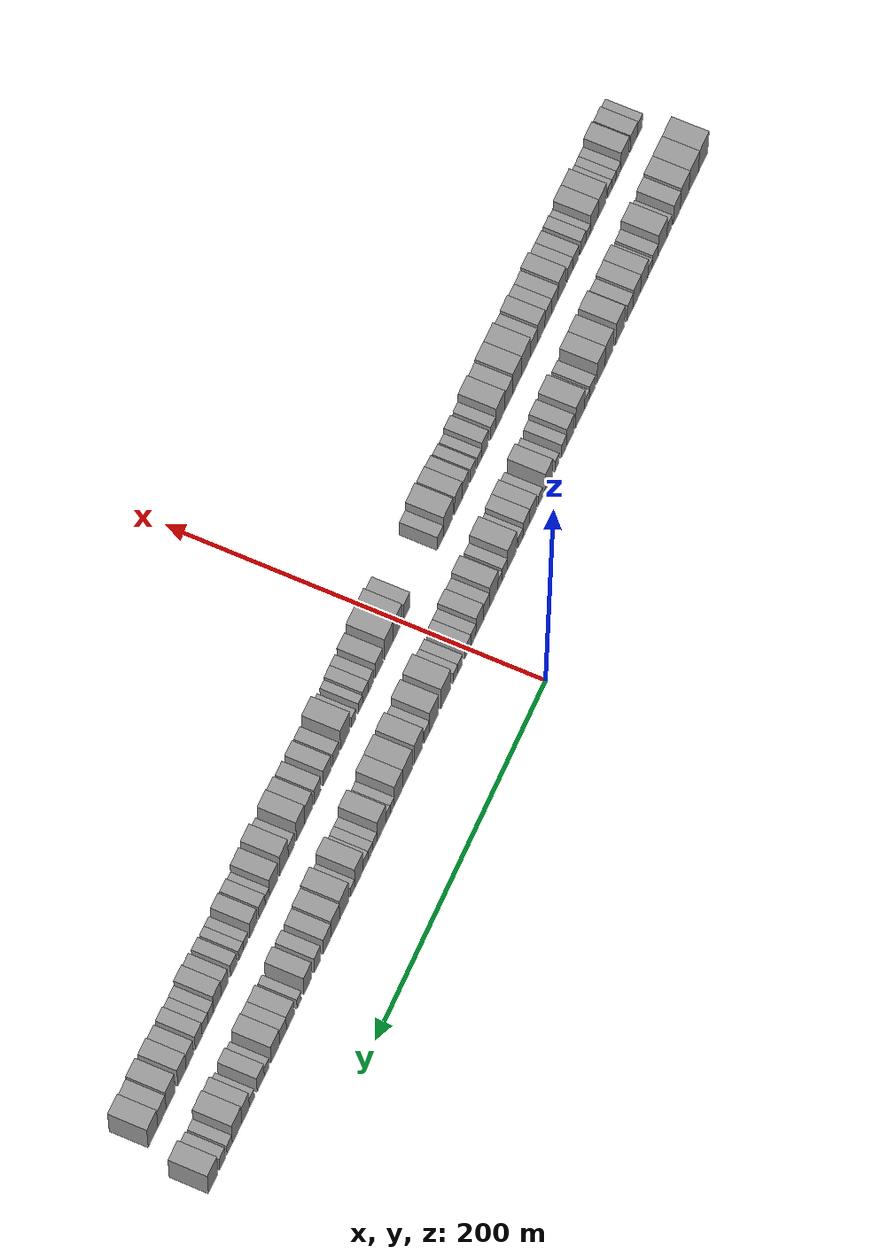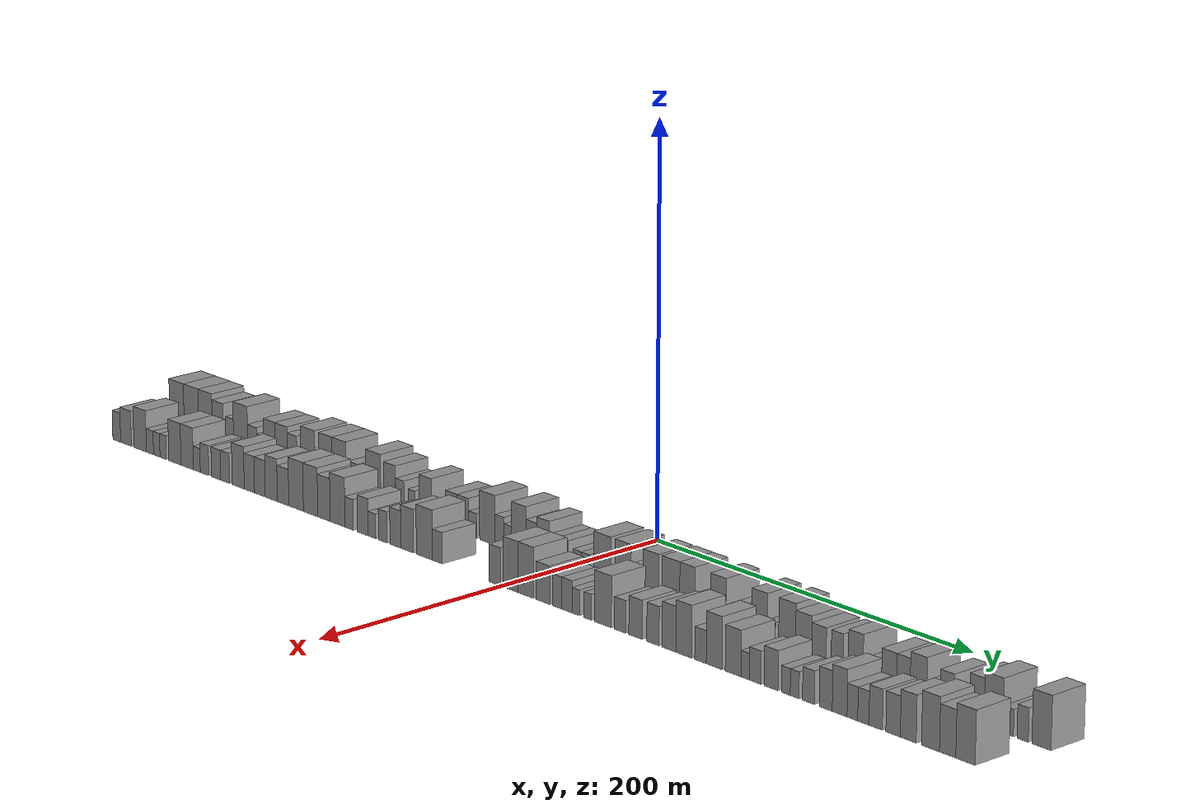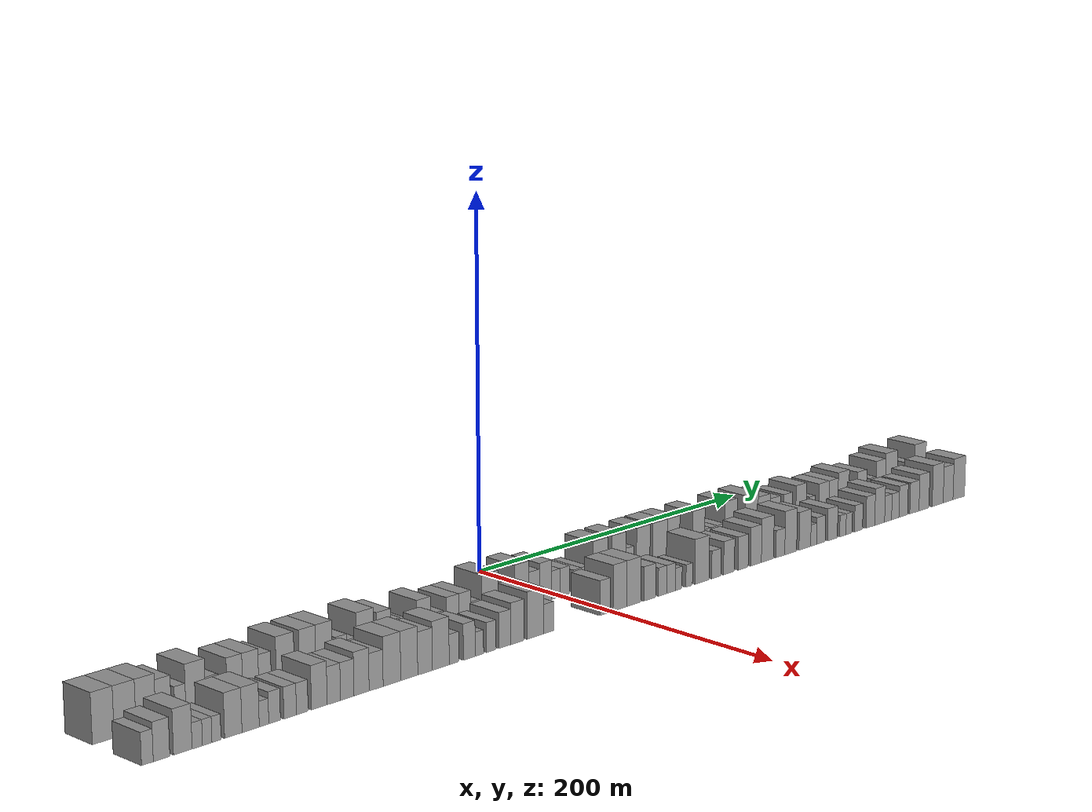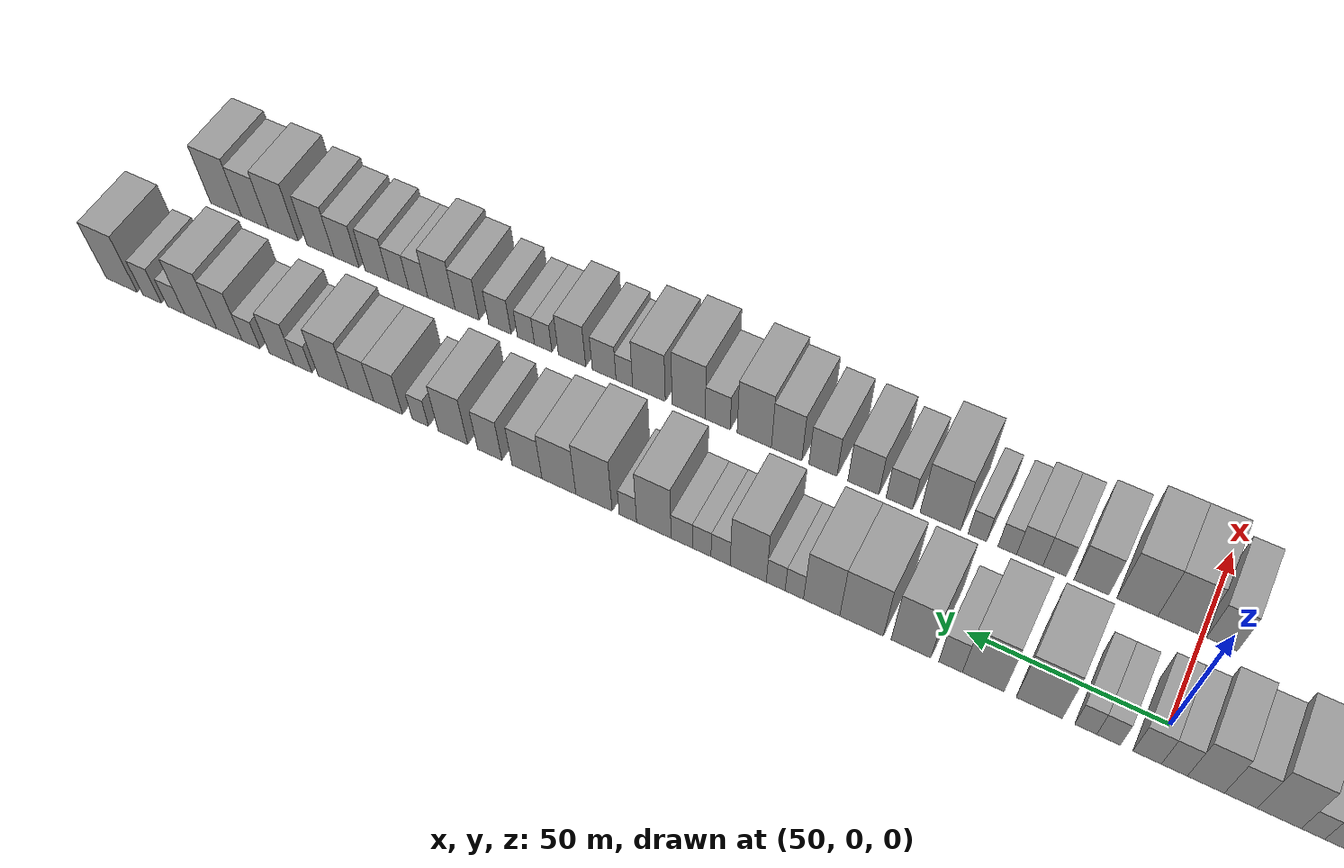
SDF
<sdf version="1.6">
 <world name="default">
  <scene>
   <sky><clouds><speed>12</speed></clouds></sky>
   <ambient>0.4 0.4 0.4 1</ambient>
   <background>0.7 0.7 0.7 1</background>
   <shadows>1</shadows>
  </scene>
  <gravity>0 0 -9.8066</gravity>
  <magnetic_field>6e-06 2.3e-05 -4.2e-05</magnetic_field>
  <physics default="0" name="default_physics" type="ode">
   <ode>
    <solver>
     <type>quick</type>
     <iters>10</iters>
     <sor>1.0</sor>
     <use_dynamic_moi_rescaling>0</use_dynamic_moi_rescaling>
    </solver>
    <constraints>
     <cfm>0</cfm>
     <erp>0.2</erp>
     <contact_max_correcting_vel>100</contact_max_correcting_vel>
     <contact_surface_layer>0.001</contact_surface_layer>
    </constraints>
   </ode>
   <max_step_size>0.004</max_step_size>
   <real_time_factor>1</real_time_factor>
   <real_time_update_rate>250</real_time_update_rate>
  </physics>
  <light name="sun" type="directional">
   <pose>0 0 10 0 0 0</pose>
   <diffuse>0.8 0.8 0.8 1</diffuse>
   <specular>0.2 0.2 0.2 1</specular>
   <attenuation>
    <range>1000</range>
    <constant>0.9</constant>
    <linear>0.01</linear>
    <quadratic>0.001</quadratic>
   </attenuation>
   <direction>-0.5 0.1 -0.9</direction>
  </light>
  <model name="building_1">
   <static>1</static>
   <pose>50.0000 -284.1602 0 0.000000 0.000000 0.000000</pose>
   <link name="link">
    <pose>0 0 12.00 0 0 0</pose>
    <collision name="collision"><geometry><box><size>20.0000 11.6795 24.0000</size></box></geometry></collision>
    <visual name="visual">
     <cast_shadows>0</cast_shadows>
     <geometry><box><size>20.0000 11.6795 24.0000</size></box></geometry>
     <material>
      <script>
       <uri>model://grey_wall/materials/scripts</uri>
       <uri>model://grey_wall/materials/textures</uri>
       <name>vrc/grey_wall</name>
      </script>
     </material>
    </visual>
   </link>
  </model>
  <model name="building_2">
   <static>1</static>
   <pose>50.0000 -272.4038 0 0.000000 0.000000 0.000000</pose>
   <link name="link">
    <pose>0 0 12.00 0 0 0</pose>
    <collision name="collision"><geometry><box><size>20.0000 11.8333 24.0000</size></box></geometry></collision>
    <visual name="visual">
     <cast_shadows>0</cast_shadows>
     <geometry><box><size>20.0000 11.8333 24.0000</size></box></geometry>
     <material>
      <script>
       <uri>model://grey_wall/materials/scripts</uri>
       <uri>model://grey_wall/materials/textures</uri>
       <name>vrc/grey_wall</name>
      </script>
     </material>
    </visual>
   </link>
  </model>
  <model name="building_3">
   <static>1</static>
   <pose>50.0000 -261.0836 0 0.000000 0.000000 0.000000</pose>
   <link name="link">
    <pose>0 0 12.00 0 0 0</pose>
    <collision name="collision"><geometry><box><size>20.0000 10.8070 24.0000</size></box></geometry></collision>
    <visual name="visual">
     <cast_shadows>0</cast_shadows>
     <geometry><box><size>20.0000 10.8070 24.0000</size></box></geometry>
     <material>
      <script>
       <uri>model://grey_wall/materials/scripts</uri>
       <uri>model://grey_wall/materials/textures</uri>
       <name>vrc/grey_wall</name>
      </script>
     </material>
    </visual>
   </link>
  </model>
  <model name="building_4">
   <static>1</static>
   <pose>50.0000 -251.3579 0 0.000000 0.000000 0.000000</pose>
   <link name="link">
    <pose>0 0 10.50 0 0 0</pose>
    <collision name="collision"><geometry><box><size>20.0000 8.6444 21.0000</size></box></geometry></collision>
    <visual name="visual">
     <cast_shadows>0</cast_shadows>
     <geometry><box><size>20.0000 8.6444 21.0000</size></box></geometry>
     <material>
      <script>
       <uri>model://grey_wall/materials/scripts</uri>
       <uri>model://grey_wall/materials/textures</uri>
       <name>vrc/grey_wall</name>
      </script>
     </material>
    </visual>
   </link>
  </model>
  <model name="building_5">
   <static>1</static>
   <pose>50.0000 -241.9757 0 0.000000 0.000000 0.000000</pose>
   <link name="link">
    <pose>0 0 7.50 0 0 0</pose>
    <collision name="collision"><geometry><box><size>20.0000 6.1200 15.0000</size></box></geometry></collision>
    <visual name="visual">
     <cast_shadows>0</cast_shadows>
     <geometry><box><size>20.0000 6.1200 15.0000</size></box></geometry>
     <material>
      <script>
       <uri>model://grey_wall/materials/scripts</uri>
       <uri>model://grey_wall/materials/textures</uri>
       <name>vrc/grey_wall</name>
      </script>
     </material>
    </visual>
   </link>
  </model>
  <model name="building_6">
   <static>1</static>
   <pose>50.0000 -233.3348 0 0.000000 0.000000 0.000000</pose>
   <link name="link">
    <pose>0 0 12.00 0 0 0</pose>
    <collision name="collision"><geometry><box><size>20.0000 11.1619 24.0000</size></box></geometry></collision>
    <visual name="visual">
     <cast_shadows>0</cast_shadows>
     <geometry><box><size>20.0000 11.1619 24.0000</size></box></geometry>
     <material>
      <script>
       <uri>model://grey_wall/materials/scripts</uri>
       <uri>model://grey_wall/materials/textures</uri>
       <name>vrc/grey_wall</name>
      </script>
     </material>
    </visual>
   </link>
  </model>
  <model name="building_7">
   <static>1</static>
   <pose>50.0000 -224.3012 0 0.000000 0.000000 0.000000</pose>
   <link name="link">
    <pose>0 0 7.50 0 0 0</pose>
    <collision name="collision"><geometry><box><size>20.0000 6.9053 15.0000</size></box></geometry></collision>
    <visual name="visual">
     <cast_shadows>0</cast_shadows>
     <geometry><box><size>20.0000 6.9053 15.0000</size></box></geometry>
     <material>
      <script>
       <uri>model://grey_wall/materials/scripts</uri>
       <uri>model://grey_wall/materials/textures</uri>
       <name>vrc/grey_wall</name>
      </script>
     </material>
    </visual>
   </link>
  </model>
  <model name="building_8">
   <static>1</static>
   <pose>50.0000 -218.1697 0 0.000000 0.000000 0.000000</pose>
   <link name="link">
    <pose>0 0 6.00 0 0 0</pose>
    <collision name="collision"><geometry><box><size>20.0000 5.3576 12.0000</size></box></geometry></collision>
    <visual name="visual">
     <cast_shadows>0</cast_shadows>
     <geometry><box><size>20.0000 5.3576 12.0000</size></box></geometry>
     <material>
      <script>
       <uri>model://grey_wall/materials/scripts</uri>
       <uri>model://grey_wall/materials/textures</uri>
       <name>vrc/grey_wall</name>
      </script>
     </material>
    </visual>
   </link>
  </model>
  <model name="building_9">
   <static>1</static>
   <pose>50.0000 -210.9690 0 0.000000 0.000000 0.000000</pose>
   <link name="link">
    <pose>0 0 10.50 0 0 0</pose>
    <collision name="collision"><geometry><box><size>20.0000 9.0439 21.0000</size></box></geometry></collision>
    <visual name="visual">
     <cast_shadows>0</cast_shadows>
     <geometry><box><size>20.0000 9.0439 21.0000</size></box></geometry>
     <material>
      <script>
       <uri>model://grey_wall/materials/scripts</uri>
       <uri>model://grey_wall/materials/textures</uri>
       <name>vrc/grey_wall</name>
      </script>
     </material>
    </visual>
   </link>
  </model>
  <model name="building_10">
   <static>1</static>
   <pose>50.0000 -201.7612 0 0.000000 0.000000 0.000000</pose>
   <link name="link">
    <pose>0 0 10.50 0 0 0</pose>
    <collision name="collision"><geometry><box><size>20.0000 9.3718 21.0000</size></box></geometry></collision>
    <visual name="visual">
     <cast_shadows>0</cast_shadows>
     <geometry><box><size>20.0000 9.3718 21.0000</size></box></geometry>
     <material>
      <script>
       <uri>model://grey_wall/materials/scripts</uri>
       <uri>model://grey_wall/materials/textures</uri>
       <name>vrc/grey_wall</name>
      </script>
     </material>
    </visual>
   </link>
  </model>
  <model name="building_11">
   <static>1</static>
   <pose>50.0000 -193.3830 0 0.000000 0.000000 0.000000</pose>
   <link name="link">
    <pose>0 0 9.00 0 0 0</pose>
    <collision name="collision"><geometry><box><size>20.0000 7.3846 18.0000</size></box></geometry></collision>
    <visual name="visual">
     <cast_shadows>0</cast_shadows>
     <geometry><box><size>20.0000 7.3846 18.0000</size></box></geometry>
     <material>
      <script>
       <uri>model://grey_wall/materials/scripts</uri>
       <uri>model://grey_wall/materials/textures</uri>
       <name>vrc/grey_wall</name>
      </script>
     </material>
    </visual>
   </link>
  </model>
  <model name="building_12">
   <static>1</static>
   <pose>50.0000 -181.2933 0 0.000000 0.000000 0.000000</pose>
   <link name="link">
    <pose>0 0 12.00 0 0 0</pose>
    <collision name="collision"><geometry><box><size>20.0000 10.7947 24.0000</size></box></geometry></collision>
    <visual name="visual">
     <cast_shadows>0</cast_shadows>
     <geometry><box><size>20.0000 10.7947 24.0000</size></box></geometry>
     <material>
      <script>
       <uri>model://grey_wall/materials/scripts</uri>
       <uri>model://grey_wall/materials/textures</uri>
       <name>vrc/grey_wall</name>
      </script>
     </material>
    </visual>
   </link>
  </model>
  <model name="building_13">
   <static>1</static>
   <pose>50.0000 -167.8822 0 0.000000 0.000000 0.000000</pose>
   <link name="link">
    <pose>0 0 12.00 0 0 0</pose>
    <collision name="collision"><geometry><box><size>20.0000 10.0277 24.0000</size></box></geometry></collision>
    <visual name="visual">
     <cast_shadows>0</cast_shadows>
     <geometry><box><size>20.0000 10.0277 24.0000</size></box></geometry>
     <material>
      <script>
       <uri>model://grey_wall/materials/scripts</uri>
       <uri>model://grey_wall/materials/textures</uri>
       <name>vrc/grey_wall</name>
      </script>
     </material>
    </visual>
   </link>
  </model>
  <model name="building_14">
   <static>1</static>
   <pose>50.0000 -157.8020 0 0.000000 0.000000 0.000000</pose>
   <link name="link">
    <pose>0 0 12.00 0 0 0</pose>
    <collision name="collision"><geometry><box><size>20.0000 10.1326 24.0000</size></box></geometry></collision>
    <visual name="visual">
     <cast_shadows>0</cast_shadows>
     <geometry><box><size>20.0000 10.1326 24.0000</size></box></geometry>
     <material>
      <script>
       <uri>model://grey_wall/materials/scripts</uri>
       <uri>model://grey_wall/materials/textures</uri>
       <name>vrc/grey_wall</name>
      </script>
     </material>
    </visual>
   </link>
  </model>
  <model name="building_15">
   <static>1</static>
   <pose>50.0000 -147.2319 0 0.000000 0.000000 0.000000</pose>
   <link name="link">
    <pose>0 0 7.50 0 0 0</pose>
    <collision name="collision"><geometry><box><size>20.0000 7.0075 15.0000</size></box></geometry></collision>
    <visual name="visual">
     <cast_shadows>0</cast_shadows>
     <geometry><box><size>20.0000 7.0075 15.0000</size></box></geometry>
     <material>
      <script>
       <uri>model://grey_wall/materials/scripts</uri>
       <uri>model://grey_wall/materials/textures</uri>
       <name>vrc/grey_wall</name>
      </script>
     </material>
    </visual>
   </link>
  </model>
  <model name="building_16">
   <static>1</static>
   <pose>50.0000 -140.7398 0 0.000000 0.000000 0.000000</pose>
   <link name="link">
    <pose>0 0 6.00 0 0 0</pose>
    <collision name="collision"><geometry><box><size>20.0000 5.9767 12.0000</size></box></geometry></collision>
    <visual name="visual">
     <cast_shadows>0</cast_shadows>
     <geometry><box><size>20.0000 5.9767 12.0000</size></box></geometry>
     <material>
      <script>
       <uri>model://grey_wall/materials/scripts</uri>
       <uri>model://grey_wall/materials/textures</uri>
       <name>vrc/grey_wall</name>
      </script>
     </material>
    </visual>
   </link>
  </model>
  <model name="building_17">
   <static>1</static>
   <pose>50.0000 -132.2860 0 0.000000 0.000000 0.000000</pose>
   <link name="link">
    <pose>0 0 12.00 0 0 0</pose>
    <collision name="collision"><geometry><box><size>20.0000 10.9309 24.0000</size></box></geometry></collision>
    <visual name="visual">
     <cast_shadows>0</cast_shadows>
     <geometry><box><size>20.0000 10.9309 24.0000</size></box></geometry>
     <material>
      <script>
       <uri>model://grey_wall/materials/scripts</uri>
       <uri>model://grey_wall/materials/textures</uri>
       <name>vrc/grey_wall</name>
      </script>
     </material>
    </visual>
   </link>
  </model>
  <model name="building_18">
   <static>1</static>
   <pose>50.0000 -120.3710 0 0.000000 0.000000 0.000000</pose>
   <link name="link">
    <pose>0 0 10.50 0 0 0</pose>
    <collision name="collision"><geometry><box><size>20.0000 8.8991 21.0000</size></box></geometry></collision>
    <visual name="visual">
     <cast_shadows>0</cast_shadows>
     <geometry><box><size>20.0000 8.8991 21.0000</size></box></geometry>
     <material>
      <script>
       <uri>model://grey_wall/materials/scripts</uri>
       <uri>model://grey_wall/materials/textures</uri>
       <name>vrc/grey_wall</name>
      </script>
     </material>
    </visual>
   </link>
  </model>
  <model name="building_19">
   <static>1</static>
   <pose>50.0000 -112.9033 0 0.000000 0.000000 0.000000</pose>
   <link name="link">
    <pose>0 0 7.50 0 0 0</pose>
    <collision name="collision"><geometry><box><size>20.0000 6.0361 15.0000</size></box></geometry></collision>
    <visual name="visual">
     <cast_shadows>0</cast_shadows>
     <geometry><box><size>20.0000 6.0361 15.0000</size></box></geometry>
     <material>
      <script>
       <uri>model://grey_wall/materials/scripts</uri>
       <uri>model://grey_wall/materials/textures</uri>
       <name>vrc/grey_wall</name>
      </script>
     </material>
    </visual>
   </link>
  </model>
  <model name="building_20">
   <static>1</static>
   <pose>50.0000 -104.4602 0 0.000000 0.000000 0.000000</pose>
   <link name="link">
    <pose>0 0 6.00 0 0 0</pose>
    <collision name="collision"><geometry><box><size>20.0000 4.8501 12.0000</size></box></geometry></collision>
    <visual name="visual">
     <cast_shadows>0</cast_shadows>
     <geometry><box><size>20.0000 4.8501 12.0000</size></box></geometry>
     <material>
      <script>
       <uri>model://grey_wall/materials/scripts</uri>
       <uri>model://grey_wall/materials/textures</uri>
       <name>vrc/grey_wall</name>
      </script>
     </material>
    </visual>
   </link>
  </model>
  <model name="building_21">
   <static>1</static>
   <pose>50.0000 -94.5433 0 0.000000 0.000000 0.000000</pose>
   <link name="link">
    <pose>0 0 10.50 0 0 0</pose>
    <collision name="collision"><geometry><box><size>20.0000 8.9838 21.0000</size></box></geometry></collision>
    <visual name="visual">
     <cast_shadows>0</cast_shadows>
     <geometry><box><size>20.0000 8.9838 21.0000</size></box></geometry>
     <material>
      <script>
       <uri>model://grey_wall/materials/scripts</uri>
       <uri>model://grey_wall/materials/textures</uri>
       <name>vrc/grey_wall</name>
      </script>
     </material>
    </visual>
   </link>
  </model>
  <model name="building_22">
   <static>1</static>
   <pose>50.0000 -84.4169 0 0.000000 0.000000 0.000000</pose>
   <link name="link">
    <pose>0 0 6.00 0 0 0</pose>
    <collision name="collision"><geometry><box><size>20.0000 5.2689 12.0000</size></box></geometry></collision>
    <visual name="visual">
     <cast_shadows>0</cast_shadows>
     <geometry><box><size>20.0000 5.2689 12.0000</size></box></geometry>
     <material>
      <script>
       <uri>model://grey_wall/materials/scripts</uri>
       <uri>model://grey_wall/materials/textures</uri>
       <name>vrc/grey_wall</name>
      </script>
     </material>
    </visual>
   </link>
  </model>
  <model name="building_23">
   <static>1</static>
   <pose>50.0000 -75.6403 0 0.000000 0.000000 0.000000</pose>
   <link name="link">
    <pose>0 0 9.00 0 0 0</pose>
    <collision name="collision"><geometry><box><size>20.0000 8.2843 18.0000</size></box></geometry></collision>
    <visual name="visual">
     <cast_shadows>0</cast_shadows>
     <geometry><box><size>20.0000 8.2843 18.0000</size></box></geometry>
     <material>
      <script>
       <uri>model://grey_wall/materials/scripts</uri>
       <uri>model://grey_wall/materials/textures</uri>
       <name>vrc/grey_wall</name>
      </script>
     </material>
    </visual>
   </link>
  </model>
  <model name="building_24">
   <static>1</static>
   <pose>50.0000 -67.4629 0 0.000000 0.000000 0.000000</pose>
   <link name="link">
    <pose>0 0 9.00 0 0 0</pose>
    <collision name="collision"><geometry><box><size>20.0000 8.0704 18.0000</size></box></geometry></collision>
    <visual name="visual">
     <cast_shadows>0</cast_shadows>
     <geometry><box><size>20.0000 8.0704 18.0000</size></box></geometry>
     <material>
      <script>
       <uri>model://grey_wall/materials/scripts</uri>
       <uri>model://grey_wall/materials/textures</uri>
       <name>vrc/grey_wall</name>
      </script>
     </material>
    </visual>
   </link>
  </model>
  <model name="building_25">
   <static>1</static>
   <pose>50.0000 -60.5944 0 0.000000 0.000000 0.000000</pose>
   <link name="link">
    <pose>0 0 6.00 0 0 0</pose>
    <collision name="collision"><geometry><box><size>20.0000 5.6667 12.0000</size></box></geometry></collision>
    <visual name="visual">
     <cast_shadows>0</cast_shadows>
     <geometry><box><size>20.0000 5.6667 12.0000</size></box></geometry>
     <material>
      <script>
       <uri>model://grey_wall/materials/scripts</uri>
       <uri>model://grey_wall/materials/textures</uri>
       <name>vrc/grey_wall</name>
      </script>
     </material>
    </visual>
   </link>
  </model>
  <model name="building_26">
   <static>1</static>
   <pose>50.0000 -50.2685 0 0.000000 0.000000 0.000000</pose>
   <link name="link">
    <pose>0 0 12.00 0 0 0</pose>
    <collision name="collision"><geometry><box><size>20.0000 10.9852 24.0000</size></box></geometry></collision>
    <visual name="visual">
     <cast_shadows>0</cast_shadows>
     <geometry><box><size>20.0000 10.9852 24.0000</size></box></geometry>
     <material>
      <script>
       <uri>model://grey_wall/materials/scripts</uri>
       <uri>model://grey_wall/materials/textures</uri>
       <name>vrc/grey_wall</name>
      </script>
     </material>
    </visual>
   </link>
  </model>
  <model name="building_27">
   <static>1</static>
   <pose>50.0000 -41.7506 0 0.000000 0.000000 0.000000</pose>
   <link name="link">
    <pose>0 0 7.50 0 0 0</pose>
    <collision name="collision"><geometry><box><size>20.0000 6.0505 15.0000</size></box></geometry></collision>
    <visual name="visual">
     <cast_shadows>0</cast_shadows>
     <geometry><box><size>20.0000 6.0505 15.0000</size></box></geometry>
     <material>
      <script>
       <uri>model://grey_wall/materials/scripts</uri>
       <uri>model://grey_wall/materials/textures</uri>
       <name>vrc/grey_wall</name>
      </script>
     </material>
    </visual>
   </link>
  </model>
  <model name="building_28">
   <static>1</static>
   <pose>50.0000 -36.0950 0 0.000000 0.000000 0.000000</pose>
   <link name="link">
    <pose>0 0 6.00 0 0 0</pose>
    <collision name="collision"><geometry><box><size>20.0000 5.2608 12.0000</size></box></geometry></collision>
    <visual name="visual">
     <cast_shadows>0</cast_shadows>
     <geometry><box><size>20.0000 5.2608 12.0000</size></box></geometry>
     <material>
      <script>
       <uri>model://grey_wall/materials/scripts</uri>
       <uri>model://grey_wall/materials/textures</uri>
       <name>vrc/grey_wall</name>
      </script>
     </material>
    </visual>
   </link>
  </model>
  <model name="building_29">
   <static>1</static>
   <pose>50.0000 -28.4472 0 0.000000 0.000000 0.000000</pose>
   <link name="link">
    <pose>0 0 12.00 0 0 0</pose>
    <collision name="collision"><geometry><box><size>20.0000 10.0347 24.0000</size></box></geometry></collision>
    <visual name="visual">
     <cast_shadows>0</cast_shadows>
     <geometry><box><size>20.0000 10.0347 24.0000</size></box></geometry>
     <material>
      <script>
       <uri>model://grey_wall/materials/scripts</uri>
       <uri>model://grey_wall/materials/textures</uri>
       <name>vrc/grey_wall</name>
      </script>
     </material>
    </visual>
   </link>
  </model>
  <model name="building_30">
   <static>1</static>
   <pose>50.0000 -19.6835 0 0.000000 0.000000 0.000000</pose>
   <link name="link">
    <pose>0 0 9.00 0 0 0</pose>
    <collision name="collision"><geometry><box><size>20.0000 7.4927 18.0000</size></box></geometry></collision>
    <visual name="visual">
     <cast_shadows>0</cast_shadows>
     <geometry><box><size>20.0000 7.4927 18.0000</size></box></geometry>
     <material>
      <script>
       <uri>model://grey_wall/materials/scripts</uri>
       <uri>model://grey_wall/materials/textures</uri>
       <name>vrc/grey_wall</name>
      </script>
     </material>
    </visual>
   </link>
  </model>
  <model name="building_31">
   <static>1</static>
   <pose>50.0000 -11.6339 0 0.000000 0.000000 0.000000</pose>
   <link name="link">
    <pose>0 0 10.50 0 0 0</pose>
    <collision name="collision"><geometry><box><size>20.0000 8.6066 21.0000</size></box></geometry></collision>
    <visual name="visual">
     <cast_shadows>0</cast_shadows>
     <geometry><box><size>20.0000 8.6066 21.0000</size></box></geometry>
     <material>
      <script>
       <uri>model://grey_wall/materials/scripts</uri>
       <uri>model://grey_wall/materials/textures</uri>
       <name>vrc/grey_wall</name>
      </script>
     </material>
    </visual>
   </link>
  </model>
  <model name="building_32">
   <static>1</static>
   <pose>50.0000 -4.2705 0 0.000000 0.000000 0.000000</pose>
   <link name="link">
    <pose>0 0 7.50 0 0 0</pose>
    <collision name="collision"><geometry><box><size>20.0000 6.1202 15.0000</size></box></geometry></collision>
    <visual name="visual">
     <cast_shadows>0</cast_shadows>
     <geometry><box><size>20.0000 6.1202 15.0000</size></box></geometry>
     <material>
      <script>
       <uri>model://grey_wall/materials/scripts</uri>
       <uri>model://grey_wall/materials/textures</uri>
       <name>vrc/grey_wall</name>
      </script>
     </material>
    </visual>
   </link>
  </model>
  <model name="building_33">
   <static>1</static>
   <pose>50.0000 2.1707 0 0.000000 0.000000 0.000000</pose>
   <link name="link">
    <pose>0 0 7.50 0 0 0</pose>
    <collision name="collision"><geometry><box><size>20.0000 6.7621 15.0000</size></box></geometry></collision>
    <visual name="visual">
     <cast_shadows>0</cast_shadows>
     <geometry><box><size>20.0000 6.7621 15.0000</size></box></geometry>
     <material>
      <script>
       <uri>model://grey_wall/materials/scripts</uri>
       <uri>model://grey_wall/materials/textures</uri>
       <name>vrc/grey_wall</name>
      </script>
     </material>
    </visual>
   </link>
  </model>
  <model name="building_34">
   <static>1</static>
   <pose>50.0000 11.3781 0 0.000000 0.000000 0.000000</pose>
   <link name="link">
    <pose>0 0 6.00 0 0 0</pose>
    <collision name="collision"><geometry><box><size>20.0000 5.6528 12.0000</size></box></geometry></collision>
    <visual name="visual">
     <cast_shadows>0</cast_shadows>
     <geometry><box><size>20.0000 5.6528 12.0000</size></box></geometry>
     <material>
      <script>
       <uri>model://grey_wall/materials/scripts</uri>
       <uri>model://grey_wall/materials/textures</uri>
       <name>vrc/grey_wall</name>
      </script>
     </material>
    </visual>
   </link>
  </model>
  <model name="building_35">
   <static>1</static>
   <pose>50.0000 16.8766 0 0.000000 0.000000 0.000000</pose>
   <link name="link">
    <pose>0 0 6.00 0 0 0</pose>
    <collision name="collision"><geometry><box><size>20.0000 5.3441 12.0000</size></box></geometry></collision>
    <visual name="visual">
     <cast_shadows>0</cast_shadows>
     <geometry><box><size>20.0000 5.3441 12.0000</size></box></geometry>
     <material>
      <script>
       <uri>model://grey_wall/materials/scripts</uri>
       <uri>model://grey_wall/materials/textures</uri>
       <name>vrc/grey_wall</name>
      </script>
     </material>
    </visual>
   </link>
  </model>
  <model name="building_36">
   <static>1</static>
   <pose>50.0000 28.2322 0 0.000000 0.000000 0.000000</pose>
   <link name="link">
    <pose>0 0 12.00 0 0 0</pose>
    <collision name="collision"><geometry><box><size>20.0000 11.3671 24.0000</size></box></geometry></collision>
    <visual name="visual">
     <cast_shadows>0</cast_shadows>
     <geometry><box><size>20.0000 11.3671 24.0000</size></box></geometry>
     <material>
      <script>
       <uri>model://grey_wall/materials/scripts</uri>
       <uri>model://grey_wall/materials/textures</uri>
       <name>vrc/grey_wall</name>
      </script>
     </material>
    </visual>
   </link>
  </model>
  <model name="building_37">
   <static>1</static>
   <pose>50.0000 42.1491 0 0.000000 0.000000 0.000000</pose>
   <link name="link">
    <pose>0 0 12.00 0 0 0</pose>
    <collision name="collision"><geometry><box><size>20.0000 10.4667 24.0000</size></box></geometry></collision>
    <visual name="visual">
     <cast_shadows>0</cast_shadows>
     <geometry><box><size>20.0000 10.4667 24.0000</size></box></geometry>
     <material>
      <script>
       <uri>model://grey_wall/materials/scripts</uri>
       <uri>model://grey_wall/materials/textures</uri>
       <name>vrc/grey_wall</name>
      </script>
     </material>
    </visual>
   </link>
  </model>
  <model name="building_38">
   <static>1</static>
   <pose>50.0000 50.3869 0 0.000000 0.000000 0.000000</pose>
   <link name="link">
    <pose>0 0 7.50 0 0 0</pose>
    <collision name="collision"><geometry><box><size>20.0000 6.0088 15.0000</size></box></geometry></collision>
    <visual name="visual">
     <cast_shadows>0</cast_shadows>
     <geometry><box><size>20.0000 6.0088 15.0000</size></box></geometry>
     <material>
      <script>
       <uri>model://grey_wall/materials/scripts</uri>
       <uri>model://grey_wall/materials/textures</uri>
       <name>vrc/grey_wall</name>
      </script>
     </material>
    </visual>
   </link>
  </model>
  <model name="building_39">
   <static>1</static>
   <pose>50.0000 60.5016 0 0.000000 0.000000 0.000000</pose>
   <link name="link">
    <pose>0 0 12.00 0 0 0</pose>
    <collision name="collision"><geometry><box><size>20.0000 10.2207 24.0000</size></box></geometry></collision>
    <visual name="visual">
     <cast_shadows>0</cast_shadows>
     <geometry><box><size>20.0000 10.2207 24.0000</size></box></geometry>
     <material>
      <script>
       <uri>model://grey_wall/materials/scripts</uri>
       <uri>model://grey_wall/materials/textures</uri>
       <name>vrc/grey_wall</name>
      </script>
     </material>
    </visual>
   </link>
  </model>
  <model name="building_40">
   <static>1</static>
   <pose>50.0000 73.3194 0 0.000000 0.000000 0.000000</pose>
   <link name="link">
    <pose>0 0 12.00 0 0 0</pose>
    <collision name="collision"><geometry><box><size>20.0000 11.4149 24.0000</size></box></geometry></collision>
    <visual name="visual">
     <cast_shadows>0</cast_shadows>
     <geometry><box><size>20.0000 11.4149 24.0000</size></box></geometry>
     <material>
      <script>
       <uri>model://grey_wall/materials/scripts</uri>
       <uri>model://grey_wall/materials/textures</uri>
       <name>vrc/grey_wall</name>
      </script>
     </material>
    </visual>
   </link>
  </model>
  <model name="building_41">
   <static>1</static>
   <pose>50.0000 83.8355 0 0.000000 0.000000 0.000000</pose>
   <link name="link">
    <pose>0 0 12.00 0 0 0</pose>
    <collision name="collision"><geometry><box><size>20.0000 9.6173 24.0000</size></box></geometry></collision>
    <visual name="visual">
     <cast_shadows>0</cast_shadows>
     <geometry><box><size>20.0000 9.6173 24.0000</size></box></geometry>
     <material>
      <script>
       <uri>model://grey_wall/materials/scripts</uri>
       <uri>model://grey_wall/materials/textures</uri>
       <name>vrc/grey_wall</name>
      </script>
     </material>
    </visual>
   </link>
  </model>
  <model name="building_42">
   <static>1</static>
   <pose>50.0000 91.1085 0 0.000000 0.000000 0.000000</pose>
   <link name="link">
    <pose>0 0 6.00 0 0 0</pose>
    <collision name="collision"><geometry><box><size>20.0000 4.9288 12.0000</size></box></geometry></collision>
    <visual name="visual">
     <cast_shadows>0</cast_shadows>
     <geometry><box><size>20.0000 4.9288 12.0000</size></box></geometry>
     <material>
      <script>
       <uri>model://grey_wall/materials/scripts</uri>
       <uri>model://grey_wall/materials/textures</uri>
       <name>vrc/grey_wall</name>
      </script>
     </material>
    </visual>
   </link>
  </model>
  <model name="building_43">
   <static>1</static>
   <pose>50.0000 96.1095 0 0.000000 0.000000 0.000000</pose>
   <link name="link">
    <pose>0 0 6.00 0 0 0</pose>
    <collision name="collision"><geometry><box><size>20.0000 5.0732 12.0000</size></box></geometry></collision>
    <visual name="visual">
     <cast_shadows>0</cast_shadows>
     <geometry><box><size>20.0000 5.0732 12.0000</size></box></geometry>
     <material>
      <script>
       <uri>model://grey_wall/materials/scripts</uri>
       <uri>model://grey_wall/materials/textures</uri>
       <name>vrc/grey_wall</name>
      </script>
     </material>
    </visual>
   </link>
  </model>
  <model name="building_44">
   <static>1</static>
   <pose>50.0000 103.5776 0 0.000000 0.000000 0.000000</pose>
   <link name="link">
    <pose>0 0 12.00 0 0 0</pose>
    <collision name="collision"><geometry><box><size>20.0000 9.8629 24.0000</size></box></geometry></collision>
    <visual name="visual">
     <cast_shadows>0</cast_shadows>
     <geometry><box><size>20.0000 9.8629 24.0000</size></box></geometry>
     <material>
      <script>
       <uri>model://grey_wall/materials/scripts</uri>
       <uri>model://grey_wall/materials/textures</uri>
       <name>vrc/grey_wall</name>
      </script>
     </material>
    </visual>
   </link>
  </model>
  <model name="building_45">
   <static>1</static>
   <pose>50.0000 111.1293 0 0.000000 0.000000 0.000000</pose>
   <link name="link">
    <pose>0 0 6.00 0 0 0</pose>
    <collision name="collision"><geometry><box><size>20.0000 5.2404 12.0000</size></box></geometry></collision>
    <visual name="visual">
     <cast_shadows>0</cast_shadows>
     <geometry><box><size>20.0000 5.2404 12.0000</size></box></geometry>
     <material>
      <script>
       <uri>model://grey_wall/materials/scripts</uri>
       <uri>model://grey_wall/materials/textures</uri>
       <name>vrc/grey_wall</name>
      </script>
     </material>
    </visual>
   </link>
  </model>
  <model name="building_46">
   <static>1</static>
   <pose>50.0000 116.3357 0 0.000000 0.000000 0.000000</pose>
   <link name="link">
    <pose>0 0 6.00 0 0 0</pose>
    <collision name="collision"><geometry><box><size>20.0000 5.1725 12.0000</size></box></geometry></collision>
    <visual name="visual">
     <cast_shadows>0</cast_shadows>
     <geometry><box><size>20.0000 5.1725 12.0000</size></box></geometry>
     <material>
      <script>
       <uri>model://grey_wall/materials/scripts</uri>
       <uri>model://grey_wall/materials/textures</uri>
       <name>vrc/grey_wall</name>
      </script>
     </material>
    </visual>
   </link>
  </model>
  <model name="building_47">
   <static>1</static>
   <pose>50.0000 121.8743 0 0.000000 0.000000 0.000000</pose>
   <link name="link">
    <pose>0 0 6.00 0 0 0</pose>
    <collision name="collision"><geometry><box><size>20.0000 5.9047 12.0000</size></box></geometry></collision>
    <visual name="visual">
     <cast_shadows>0</cast_shadows>
     <geometry><box><size>20.0000 5.9047 12.0000</size></box></geometry>
     <material>
      <script>
       <uri>model://grey_wall/materials/scripts</uri>
       <uri>model://grey_wall/materials/textures</uri>
       <name>vrc/grey_wall</name>
      </script>
     </material>
    </visual>
   </link>
  </model>
  <model name="building_48">
   <static>1</static>
   <pose>50.0000 129.6928 0 0.000000 0.000000 0.000000</pose>
   <link name="link">
    <pose>0 0 12.00 0 0 0</pose>
    <collision name="collision"><geometry><box><size>20.0000 9.7323 24.0000</size></box></geometry></collision>
    <visual name="visual">
     <cast_shadows>0</cast_shadows>
     <geometry><box><size>20.0000 9.7323 24.0000</size></box></geometry>
     <material>
      <script>
       <uri>model://grey_wall/materials/scripts</uri>
       <uri>model://grey_wall/materials/textures</uri>
       <name>vrc/grey_wall</name>
      </script>
     </material>
    </visual>
   </link>
  </model>
  <model name="building_49">
   <static>1</static>
   <pose>50.0000 137.0227 0 0.000000 0.000000 0.000000</pose>
   <link name="link">
    <pose>0 0 6.00 0 0 0</pose>
    <collision name="collision"><geometry><box><size>20.0000 4.9277 12.0000</size></box></geometry></collision>
    <visual name="visual">
     <cast_shadows>0</cast_shadows>
     <geometry><box><size>20.0000 4.9277 12.0000</size></box></geometry>
     <material>
      <script>
       <uri>model://grey_wall/materials/scripts</uri>
       <uri>model://grey_wall/materials/textures</uri>
       <name>vrc/grey_wall</name>
      </script>
     </material>
    </visual>
   </link>
  </model>
  <model name="building_50">
   <static>1</static>
   <pose>50.0000 146.7251 0 0.000000 0.000000 0.000000</pose>
   <link name="link">
    <pose>0 0 12.00 0 0 0</pose>
    <collision name="collision"><geometry><box><size>20.0000 10.4770 24.0000</size></box></geometry></collision>
    <visual name="visual">
     <cast_shadows>0</cast_shadows>
     <geometry><box><size>20.0000 10.4770 24.0000</size></box></geometry>
     <material>
      <script>
       <uri>model://grey_wall/materials/scripts</uri>
       <uri>model://grey_wall/materials/textures</uri>
       <name>vrc/grey_wall</name>
      </script>
     </material>
    </visual>
   </link>
  </model>
  <model name="building_51">
   <static>1</static>
   <pose>50.0000 156.9101 0 0.000000 0.000000 0.000000</pose>
   <link name="link">
    <pose>0 0 10.50 0 0 0</pose>
    <collision name="collision"><geometry><box><size>20.0000 9.8931 21.0000</size></box></geometry></collision>
    <visual name="visual">
     <cast_shadows>0</cast_shadows>
     <geometry><box><size>20.0000 9.8931 21.0000</size></box></geometry>
     <material>
      <script>
       <uri>model://grey_wall/materials/scripts</uri>
       <uri>model://grey_wall/materials/textures</uri>
       <name>vrc/grey_wall</name>
      </script>
     </material>
    </visual>
   </link>
  </model>
  <model name="building_52">
   <static>1</static>
   <pose>50.0000 166.2737 0 0.000000 0.000000 0.000000</pose>
   <link name="link">
    <pose>0 0 9.00 0 0 0</pose>
    <collision name="collision"><geometry><box><size>20.0000 8.8340 18.0000</size></box></geometry></collision>
    <visual name="visual">
     <cast_shadows>0</cast_shadows>
     <geometry><box><size>20.0000 8.8340 18.0000</size></box></geometry>
     <material>
      <script>
       <uri>model://grey_wall/materials/scripts</uri>
       <uri>model://grey_wall/materials/textures</uri>
       <name>vrc/grey_wall</name>
      </script>
     </material>
    </visual>
   </link>
  </model>
  <model name="building_53">
   <static>1</static>
   <pose>50.0000 177.3260 0 0.000000 0.000000 0.000000</pose>
   <link name="link">
    <pose>0 0 9.00 0 0 0</pose>
    <collision name="collision"><geometry><box><size>20.0000 7.2707 18.0000</size></box></geometry></collision>
    <visual name="visual">
     <cast_shadows>0</cast_shadows>
     <geometry><box><size>20.0000 7.2707 18.0000</size></box></geometry>
     <material>
      <script>
       <uri>model://grey_wall/materials/scripts</uri>
       <uri>model://grey_wall/materials/textures</uri>
       <name>vrc/grey_wall</name>
      </script>
     </material>
    </visual>
   </link>
  </model>
  <model name="building_54">
   <static>1</static>
   <pose>50.0000 188.4269 0 0.000000 0.000000 0.000000</pose>
   <link name="link">
    <pose>0 0 10.50 0 0 0</pose>
    <collision name="collision"><geometry><box><size>20.0000 8.9310 21.0000</size></box></geometry></collision>
    <visual name="visual">
     <cast_shadows>0</cast_shadows>
     <geometry><box><size>20.0000 8.9310 21.0000</size></box></geometry>
     <material>
      <script>
       <uri>model://grey_wall/materials/scripts</uri>
       <uri>model://grey_wall/materials/textures</uri>
       <name>vrc/grey_wall</name>
      </script>
     </material>
    </visual>
   </link>
  </model>
  <model name="building_55">
   <static>1</static>
   <pose>50.0000 198.3898 0 0.000000 0.000000 0.000000</pose>
   <link name="link">
    <pose>0 0 6.00 0 0 0</pose>
    <collision name="collision"><geometry><box><size>20.0000 4.9948 12.0000</size></box></geometry></collision>
    <visual name="visual">
     <cast_shadows>0</cast_shadows>
     <geometry><box><size>20.0000 4.9948 12.0000</size></box></geometry>
     <material>
      <script>
       <uri>model://grey_wall/materials/scripts</uri>
       <uri>model://grey_wall/materials/textures</uri>
       <name>vrc/grey_wall</name>
      </script>
     </material>
    </visual>
   </link>
  </model>
  <model name="building_56">
   <static>1</static>
   <pose>50.0000 208.3783 0 0.000000 0.000000 0.000000</pose>
   <link name="link">
    <pose>0 0 9.00 0 0 0</pose>
    <collision name="collision"><geometry><box><size>20.0000 8.9823 18.0000</size></box></geometry></collision>
    <visual name="visual">
     <cast_shadows>0</cast_shadows>
     <geometry><box><size>20.0000 8.9823 18.0000</size></box></geometry>
     <material>
      <script>
       <uri>model://grey_wall/materials/scripts</uri>
       <uri>model://grey_wall/materials/textures</uri>
       <name>vrc/grey_wall</name>
      </script>
     </material>
    </visual>
   </link>
  </model>
  <model name="building_57">
   <static>1</static>
   <pose>50.0000 216.7896 0 0.000000 0.000000 0.000000</pose>
   <link name="link">
    <pose>0 0 9.00 0 0 0</pose>
    <collision name="collision"><geometry><box><size>20.0000 7.8402 18.0000</size></box></geometry></collision>
    <visual name="visual">
     <cast_shadows>0</cast_shadows>
     <geometry><box><size>20.0000 7.8402 18.0000</size></box></geometry>
     <material>
      <script>
       <uri>model://grey_wall/materials/scripts</uri>
       <uri>model://grey_wall/materials/textures</uri>
       <name>vrc/grey_wall</name>
      </script>
     </material>
    </visual>
   </link>
  </model>
  <model name="building_58">
   <static>1</static>
   <pose>50.0000 225.5620 0 0.000000 0.000000 0.000000</pose>
   <link name="link">
    <pose>0 0 10.50 0 0 0</pose>
    <collision name="collision"><geometry><box><size>20.0000 9.7047 21.0000</size></box></geometry></collision>
    <visual name="visual">
     <cast_shadows>0</cast_shadows>
     <geometry><box><size>20.0000 9.7047 21.0000</size></box></geometry>
     <material>
      <script>
       <uri>model://grey_wall/materials/scripts</uri>
       <uri>model://grey_wall/materials/textures</uri>
       <name>vrc/grey_wall</name>
      </script>
     </material>
    </visual>
   </link>
  </model>
  <model name="building_59">
   <static>1</static>
   <pose>50.0000 235.2717 0 0.000000 0.000000 0.000000</pose>
   <link name="link">
    <pose>0 0 6.00 0 0 0</pose>
    <collision name="collision"><geometry><box><size>20.0000 5.7147 12.0000</size></box></geometry></collision>
    <visual name="visual">
     <cast_shadows>0</cast_shadows>
     <geometry><box><size>20.0000 5.7147 12.0000</size></box></geometry>
     <material>
      <script>
       <uri>model://grey_wall/materials/scripts</uri>
       <uri>model://grey_wall/materials/textures</uri>
       <name>vrc/grey_wall</name>
      </script>
     </material>
    </visual>
   </link>
  </model>
  <model name="building_60">
   <static>1</static>
   <pose>50.0000 242.1618 0 0.000000 0.000000 0.000000</pose>
   <link name="link">
    <pose>0 0 9.00 0 0 0</pose>
    <collision name="collision"><geometry><box><size>20.0000 8.0655 18.0000</size></box></geometry></collision>
    <visual name="visual">
     <cast_shadows>0</cast_shadows>
     <geometry><box><size>20.0000 8.0655 18.0000</size></box></geometry>
     <material>
      <script>
       <uri>model://grey_wall/materials/scripts</uri>
       <uri>model://grey_wall/materials/textures</uri>
       <name>vrc/grey_wall</name>
      </script>
     </material>
    </visual>
   </link>
  </model>
  <model name="building_61">
   <static>1</static>
   <pose>50.0000 252.1218 0 0.000000 0.000000 0.000000</pose>
   <link name="link">
    <pose>0 0 6.00 0 0 0</pose>
    <collision name="collision"><geometry><box><size>20.0000 5.8545 12.0000</size></box></geometry></collision>
    <visual name="visual">
     <cast_shadows>0</cast_shadows>
     <geometry><box><size>20.0000 5.8545 12.0000</size></box></geometry>
     <material>
      <script>
       <uri>model://grey_wall/materials/scripts</uri>
       <uri>model://grey_wall/materials/textures</uri>
       <name>vrc/grey_wall</name>
      </script>
     </material>
    </visual>
   </link>
  </model>
  <model name="building_62">
   <static>1</static>
   <pose>50.0000 259.2946 0 0.000000 0.000000 0.000000</pose>
   <link name="link">
    <pose>0 0 10.50 0 0 0</pose>
    <collision name="collision"><geometry><box><size>20.0000 8.4913 21.0000</size></box></geometry></collision>
    <visual name="visual">
     <cast_shadows>0</cast_shadows>
     <geometry><box><size>20.0000 8.4913 21.0000</size></box></geometry>
     <material>
      <script>
       <uri>model://grey_wall/materials/scripts</uri>
       <uri>model://grey_wall/materials/textures</uri>
       <name>vrc/grey_wall</name>
      </script>
     </material>
    </visual>
   </link>
  </model>
  <model name="building_63">
   <static>1</static>
   <pose>50.0000 268.8690 0 0.000000 0.000000 0.000000</pose>
   <link name="link">
    <pose>0 0 12.00 0 0 0</pose>
    <collision name="collision"><geometry><box><size>20.0000 10.6575 24.0000</size></box></geometry></collision>
    <visual name="visual">
     <cast_shadows>0</cast_shadows>
     <geometry><box><size>20.0000 10.6575 24.0000</size></box></geometry>
     <material>
      <script>
       <uri>model://grey_wall/materials/scripts</uri>
       <uri>model://grey_wall/materials/textures</uri>
       <name>vrc/grey_wall</name>
      </script>
     </material>
    </visual>
   </link>
  </model>
  <model name="building_64">
   <static>1</static>
   <pose>50.0000 277.1738 0 0.000000 0.000000 0.000000</pose>
   <link name="link">
    <pose>0 0 6.00 0 0 0</pose>
    <collision name="collision"><geometry><box><size>20.0000 5.9520 12.0000</size></box></geometry></collision>
    <visual name="visual">
     <cast_shadows>0</cast_shadows>
     <geometry><box><size>20.0000 5.9520 12.0000</size></box></geometry>
     <material>
      <script>
       <uri>model://grey_wall/materials/scripts</uri>
       <uri>model://grey_wall/materials/textures</uri>
       <name>vrc/grey_wall</name>
      </script>
     </material>
    </visual>
   </link>
  </model>
  <model name="building_65">
   <static>1</static>
   <pose>50.0000 285.3070 0 0.000000 0.000000 0.000000</pose>
   <link name="link">
    <pose>0 0 7.50 0 0 0</pose>
    <collision name="collision"><geometry><box><size>20.0000 6.3145 15.0000</size></box></geometry></collision>
    <visual name="visual">
     <cast_shadows>0</cast_shadows>
     <geometry><box><size>20.0000 6.3145 15.0000</size></box></geometry>
     <material>
      <script>
       <uri>model://grey_wall/materials/scripts</uri>
       <uri>model://grey_wall/materials/textures</uri>
       <name>vrc/grey_wall</name>
      </script>
     </material>
    </visual>
   </link>
  </model>
  <model name="building_66">
   <static>1</static>
   <pose>50.0000 295.7651 0 0.000000 0.000000 0.000000</pose>
   <link name="link">
    <pose>0 0 12.00 0 0 0</pose>
    <collision name="collision"><geometry><box><size>20.0000 10.6016 24.0000</size></box></geometry></collision>
    <visual name="visual">
     <cast_shadows>0</cast_shadows>
     <geometry><box><size>20.0000 10.6016 24.0000</size></box></geometry>
     <material>
      <script>
       <uri>model://grey_wall/materials/scripts</uri>
       <uri>model://grey_wall/materials/textures</uri>
       <name>vrc/grey_wall</name>
      </script>
     </material>
    </visual>
   </link>
  </model>
  <model name="building_67">
   <static>1</static>
   <pose>85.0000 -286.8736 0 0.000000 0.000000 0.000000</pose>
   <link name="link">
    <pose>0 0 7.50 0 0 0</pose>
    <collision name="collision"><geometry><box><size>20.0000 6.2529 15.0000</size></box></geometry></collision>
    <visual name="visual">
     <cast_shadows>0</cast_shadows>
     <geometry><box><size>20.0000 6.2529 15.0000</size></box></geometry>
     <material>
      <script>
       <uri>model://grey_wall/materials/scripts</uri>
       <uri>model://grey_wall/materials/textures</uri>
       <name>vrc/grey_wall</name>
      </script>
     </material>
    </visual>
   </link>
  </model>
  <model name="building_68">
   <static>1</static>
   <pose>85.0000 -279.3542 0 0.000000 0.000000 0.000000</pose>
   <link name="link">
    <pose>0 0 9.00 0 0 0</pose>
    <collision name="collision"><geometry><box><size>20.0000 8.7859 18.0000</size></box></geometry></collision>
    <visual name="visual">
     <cast_shadows>0</cast_shadows>
     <geometry><box><size>20.0000 8.7859 18.0000</size></box></geometry>
     <material>
      <script>
       <uri>model://grey_wall/materials/scripts</uri>
       <uri>model://grey_wall/materials/textures</uri>
       <name>vrc/grey_wall</name>
      </script>
     </material>
    </visual>
   </link>
  </model>
  <model name="building_69">
   <static>1</static>
   <pose>85.0000 -267.9315 0 0.000000 0.000000 0.000000</pose>
   <link name="link">
    <pose>0 0 10.50 0 0 0</pose>
    <collision name="collision"><geometry><box><size>20.0000 10.0595 21.0000</size></box></geometry></collision>
    <visual name="visual">
     <cast_shadows>0</cast_shadows>
     <geometry><box><size>20.0000 10.0595 21.0000</size></box></geometry>
     <material>
      <script>
       <uri>model://grey_wall/materials/scripts</uri>
       <uri>model://grey_wall/materials/textures</uri>
       <name>vrc/grey_wall</name>
      </script>
     </material>
    </visual>
   </link>
  </model>
  <model name="building_70">
   <static>1</static>
   <pose>85.0000 -260.0736 0 0.000000 0.000000 0.000000</pose>
   <link name="link">
    <pose>0 0 6.00 0 0 0</pose>
    <collision name="collision"><geometry><box><size>20.0000 5.6561 12.0000</size></box></geometry></collision>
    <visual name="visual">
     <cast_shadows>0</cast_shadows>
     <geometry><box><size>20.0000 5.6561 12.0000</size></box></geometry>
     <material>
      <script>
       <uri>model://grey_wall/materials/scripts</uri>
       <uri>model://grey_wall/materials/textures</uri>
       <name>vrc/grey_wall</name>
      </script>
     </material>
    </visual>
   </link>
  </model>
  <model name="building_71">
   <static>1</static>
   <pose>85.0000 -254.6443 0 0.000000 0.000000 0.000000</pose>
   <link name="link">
    <pose>0 0 6.00 0 0 0</pose>
    <collision name="collision"><geometry><box><size>20.0000 5.2025 12.0000</size></box></geometry></collision>
    <visual name="visual">
     <cast_shadows>0</cast_shadows>
     <geometry><box><size>20.0000 5.2025 12.0000</size></box></geometry>
     <material>
      <script>
       <uri>model://grey_wall/materials/scripts</uri>
       <uri>model://grey_wall/materials/textures</uri>
       <name>vrc/grey_wall</name>
      </script>
     </material>
    </visual>
   </link>
  </model>
  <model name="building_72">
   <static>1</static>
   <pose>85.0000 -249.5383 0 0.000000 0.000000 0.000000</pose>
   <link name="link">
    <pose>0 0 6.00 0 0 0</pose>
    <collision name="collision"><geometry><box><size>20.0000 5.0094 12.0000</size></box></geometry></collision>
    <visual name="visual">
     <cast_shadows>0</cast_shadows>
     <geometry><box><size>20.0000 5.0094 12.0000</size></box></geometry>
     <material>
      <script>
       <uri>model://grey_wall/materials/scripts</uri>
       <uri>model://grey_wall/materials/textures</uri>
       <name>vrc/grey_wall</name>
      </script>
     </material>
    </visual>
   </link>
  </model>
  <model name="building_73">
   <static>1</static>
   <pose>85.0000 -240.1807 0 0.000000 0.000000 0.000000</pose>
   <link name="link">
    <pose>0 0 10.50 0 0 0</pose>
    <collision name="collision"><geometry><box><size>20.0000 9.7058 21.0000</size></box></geometry></collision>
    <visual name="visual">
     <cast_shadows>0</cast_shadows>
     <geometry><box><size>20.0000 9.7058 21.0000</size></box></geometry>
     <material>
      <script>
       <uri>model://grey_wall/materials/scripts</uri>
       <uri>model://grey_wall/materials/textures</uri>
       <name>vrc/grey_wall</name>
      </script>
     </material>
    </visual>
   </link>
  </model>
  <model name="building_74">
   <static>1</static>
   <pose>85.0000 -230.4570 0 0.000000 0.000000 0.000000</pose>
   <link name="link">
    <pose>0 0 10.50 0 0 0</pose>
    <collision name="collision"><geometry><box><size>20.0000 9.7416 21.0000</size></box></geometry></collision>
    <visual name="visual">
     <cast_shadows>0</cast_shadows>
     <geometry><box><size>20.0000 9.7416 21.0000</size></box></geometry>
     <material>
      <script>
       <uri>model://grey_wall/materials/scripts</uri>
       <uri>model://grey_wall/materials/textures</uri>
       <name>vrc/grey_wall</name>
      </script>
     </material>
    </visual>
   </link>
  </model>
  <model name="building_75">
   <static>1</static>
   <pose>85.0000 -222.8788 0 0.000000 0.000000 0.000000</pose>
   <link name="link">
    <pose>0 0 6.00 0 0 0</pose>
    <collision name="collision"><geometry><box><size>20.0000 5.4148 12.0000</size></box></geometry></collision>
    <visual name="visual">
     <cast_shadows>0</cast_shadows>
     <geometry><box><size>20.0000 5.4148 12.0000</size></box></geometry>
     <material>
      <script>
       <uri>model://grey_wall/materials/scripts</uri>
       <uri>model://grey_wall/materials/textures</uri>
       <name>vrc/grey_wall</name>
      </script>
     </material>
    </visual>
   </link>
  </model>
  <model name="building_76">
   <static>1</static>
   <pose>85.0000 -216.8405 0 0.000000 0.000000 0.000000</pose>
   <link name="link">
    <pose>0 0 7.50 0 0 0</pose>
    <collision name="collision"><geometry><box><size>20.0000 6.6617 15.0000</size></box></geometry></collision>
    <visual name="visual">
     <cast_shadows>0</cast_shadows>
     <geometry><box><size>20.0000 6.6617 15.0000</size></box></geometry>
     <material>
      <script>
       <uri>model://grey_wall/materials/scripts</uri>
       <uri>model://grey_wall/materials/textures</uri>
       <name>vrc/grey_wall</name>
      </script>
     </material>
    </visual>
   </link>
  </model>
  <model name="building_77">
   <static>1</static>
   <pose>85.0000 -207.8749 0 0.000000 0.000000 0.000000</pose>
   <link name="link">
    <pose>0 0 7.50 0 0 0</pose>
    <collision name="collision"><geometry><box><size>20.0000 7.2696 15.0000</size></box></geometry></collision>
    <visual name="visual">
     <cast_shadows>0</cast_shadows>
     <geometry><box><size>20.0000 7.2696 15.0000</size></box></geometry>
     <material>
      <script>
       <uri>model://grey_wall/materials/scripts</uri>
       <uri>model://grey_wall/materials/textures</uri>
       <name>vrc/grey_wall</name>
      </script>
     </material>
    </visual>
   </link>
  </model>
  <model name="building_78">
   <static>1</static>
   <pose>85.0000 -200.8433 0 0.000000 0.000000 0.000000</pose>
   <link name="link">
    <pose>0 0 7.50 0 0 0</pose>
    <collision name="collision"><geometry><box><size>20.0000 6.7935 15.0000</size></box></geometry></collision>
    <visual name="visual">
     <cast_shadows>0</cast_shadows>
     <geometry><box><size>20.0000 6.7935 15.0000</size></box></geometry>
     <material>
      <script>
       <uri>model://grey_wall/materials/scripts</uri>
       <uri>model://grey_wall/materials/textures</uri>
       <name>vrc/grey_wall</name>
      </script>
     </material>
    </visual>
   </link>
  </model>
  <model name="building_79">
   <static>1</static>
   <pose>85.0000 -190.8085 0 0.000000 0.000000 0.000000</pose>
   <link name="link">
    <pose>0 0 10.50 0 0 0</pose>
    <collision name="collision"><geometry><box><size>20.0000 9.2762 21.0000</size></box></geometry></collision>
    <visual name="visual">
     <cast_shadows>0</cast_shadows>
     <geometry><box><size>20.0000 9.2762 21.0000</size></box></geometry>
     <material>
      <script>
       <uri>model://grey_wall/materials/scripts</uri>
       <uri>model://grey_wall/materials/textures</uri>
       <name>vrc/grey_wall</name>
      </script>
     </material>
    </visual>
   </link>
  </model>
  <model name="building_80">
   <static>1</static>
   <pose>85.0000 -182.1932 0 0.000000 0.000000 0.000000</pose>
   <link name="link">
    <pose>0 0 9.00 0 0 0</pose>
    <collision name="collision"><geometry><box><size>20.0000 7.9544 18.0000</size></box></geometry></collision>
    <visual name="visual">
     <cast_shadows>0</cast_shadows>
     <geometry><box><size>20.0000 7.9544 18.0000</size></box></geometry>
     <material>
      <script>
       <uri>model://grey_wall/materials/scripts</uri>
       <uri>model://grey_wall/materials/textures</uri>
       <name>vrc/grey_wall</name>
      </script>
     </material>
    </visual>
   </link>
  </model>
  <model name="building_81">
   <static>1</static>
   <pose>85.0000 -174.1691 0 0.000000 0.000000 0.000000</pose>
   <link name="link">
    <pose>0 0 9.00 0 0 0</pose>
    <collision name="collision"><geometry><box><size>20.0000 8.0937 18.0000</size></box></geometry></collision>
    <visual name="visual">
     <cast_shadows>0</cast_shadows>
     <geometry><box><size>20.0000 8.0937 18.0000</size></box></geometry>
     <material>
      <script>
       <uri>model://grey_wall/materials/scripts</uri>
       <uri>model://grey_wall/materials/textures</uri>
       <name>vrc/grey_wall</name>
      </script>
     </material>
    </visual>
   </link>
  </model>
  <model name="building_82">
   <static>1</static>
   <pose>85.0000 -165.5374 0 0.000000 0.000000 0.000000</pose>
   <link name="link">
    <pose>0 0 10.50 0 0 0</pose>
    <collision name="collision"><geometry><box><size>20.0000 9.1697 21.0000</size></box></geometry></collision>
    <visual name="visual">
     <cast_shadows>0</cast_shadows>
     <geometry><box><size>20.0000 9.1697 21.0000</size></box></geometry>
     <material>
      <script>
       <uri>model://grey_wall/materials/scripts</uri>
       <uri>model://grey_wall/materials/textures</uri>
       <name>vrc/grey_wall</name>
      </script>
     </material>
    </visual>
   </link>
  </model>
  <model name="building_83">
   <static>1</static>
   <pose>85.0000 -156.6534 0 0.000000 0.000000 0.000000</pose>
   <link name="link">
    <pose>0 0 9.00 0 0 0</pose>
    <collision name="collision"><geometry><box><size>20.0000 8.5984 18.0000</size></box></geometry></collision>
    <visual name="visual">
     <cast_shadows>0</cast_shadows>
     <geometry><box><size>20.0000 8.5984 18.0000</size></box></geometry>
     <material>
      <script>
       <uri>model://grey_wall/materials/scripts</uri>
       <uri>model://grey_wall/materials/textures</uri>
       <name>vrc/grey_wall</name>
      </script>
     </material>
    </visual>
   </link>
  </model>
  <model name="building_84">
   <static>1</static>
   <pose>85.0000 -146.9001 0 0.000000 0.000000 0.000000</pose>
   <link name="link">
    <pose>0 0 12.00 0 0 0</pose>
    <collision name="collision"><geometry><box><size>20.0000 10.9081 24.0000</size></box></geometry></collision>
    <visual name="visual">
     <cast_shadows>0</cast_shadows>
     <geometry><box><size>20.0000 10.9081 24.0000</size></box></geometry>
     <material>
      <script>
       <uri>model://grey_wall/materials/scripts</uri>
       <uri>model://grey_wall/materials/textures</uri>
       <name>vrc/grey_wall</name>
      </script>
     </material>
    </visual>
   </link>
  </model>
  <model name="building_85">
   <static>1</static>
   <pose>85.0000 -136.1205 0 0.000000 0.000000 0.000000</pose>
   <link name="link">
    <pose>0 0 12.00 0 0 0</pose>
    <collision name="collision"><geometry><box><size>20.0000 10.6510 24.0000</size></box></geometry></collision>
    <visual name="visual">
     <cast_shadows>0</cast_shadows>
     <geometry><box><size>20.0000 10.6510 24.0000</size></box></geometry>
     <material>
      <script>
       <uri>model://grey_wall/materials/scripts</uri>
       <uri>model://grey_wall/materials/textures</uri>
       <name>vrc/grey_wall</name>
      </script>
     </material>
    </visual>
   </link>
  </model>
  <model name="building_86">
   <static>1</static>
   <pose>85.0000 -126.1963 0 0.000000 0.000000 0.000000</pose>
   <link name="link">
    <pose>0 0 10.50 0 0 0</pose>
    <collision name="collision"><geometry><box><size>20.0000 9.1974 21.0000</size></box></geometry></collision>
    <visual name="visual">
     <cast_shadows>0</cast_shadows>
     <geometry><box><size>20.0000 9.1974 21.0000</size></box></geometry>
     <material>
      <script>
       <uri>model://grey_wall/materials/scripts</uri>
       <uri>model://grey_wall/materials/textures</uri>
       <name>vrc/grey_wall</name>
      </script>
     </material>
    </visual>
   </link>
  </model>
  <model name="building_87">
   <static>1</static>
   <pose>85.0000 -116.1840 0 0.000000 0.000000 0.000000</pose>
   <link name="link">
    <pose>0 0 12.00 0 0 0</pose>
    <collision name="collision"><geometry><box><size>20.0000 10.8273 24.0000</size></box></geometry></collision>
    <visual name="visual">
     <cast_shadows>0</cast_shadows>
     <geometry><box><size>20.0000 10.8273 24.0000</size></box></geometry>
     <material>
      <script>
       <uri>model://grey_wall/materials/scripts</uri>
       <uri>model://grey_wall/materials/textures</uri>
       <name>vrc/grey_wall</name>
      </script>
     </material>
    </visual>
   </link>
  </model>
  <model name="building_88">
   <static>1</static>
   <pose>85.0000 -107.6926 0 0.000000 0.000000 0.000000</pose>
   <link name="link">
    <pose>0 0 7.50 0 0 0</pose>
    <collision name="collision"><geometry><box><size>20.0000 6.1555 15.0000</size></box></geometry></collision>
    <visual name="visual">
     <cast_shadows>0</cast_shadows>
     <geometry><box><size>20.0000 6.1555 15.0000</size></box></geometry>
     <material>
      <script>
       <uri>model://grey_wall/materials/scripts</uri>
       <uri>model://grey_wall/materials/textures</uri>
       <name>vrc/grey_wall</name>
      </script>
     </material>
    </visual>
   </link>
  </model>
  <model name="building_89">
   <static>1</static>
   <pose>85.0000 -97.7616 0 0.000000 0.000000 0.000000</pose>
   <link name="link">
    <pose>0 0 9.00 0 0 0</pose>
    <collision name="collision"><geometry><box><size>20.0000 7.7066 18.0000</size></box></geometry></collision>
    <visual name="visual">
     <cast_shadows>0</cast_shadows>
     <geometry><box><size>20.0000 7.7066 18.0000</size></box></geometry>
     <material>
      <script>
       <uri>model://grey_wall/materials/scripts</uri>
       <uri>model://grey_wall/materials/textures</uri>
       <name>vrc/grey_wall</name>
      </script>
     </material>
    </visual>
   </link>
  </model>
  <model name="building_90">
   <static>1</static>
   <pose>85.0000 -91.1466 0 0.000000 0.000000 0.000000</pose>
   <link name="link">
    <pose>0 0 6.00 0 0 0</pose>
    <collision name="collision"><geometry><box><size>20.0000 5.5233 12.0000</size></box></geometry></collision>
    <visual name="visual">
     <cast_shadows>0</cast_shadows>
     <geometry><box><size>20.0000 5.5233 12.0000</size></box></geometry>
     <material>
      <script>
       <uri>model://grey_wall/materials/scripts</uri>
       <uri>model://grey_wall/materials/textures</uri>
       <name>vrc/grey_wall</name>
      </script>
     </material>
    </visual>
   </link>
  </model>
  <model name="building_91">
   <static>1</static>
   <pose>85.0000 -83.2676 0 0.000000 0.000000 0.000000</pose>
   <link name="link">
    <pose>0 0 7.50 0 0 0</pose>
    <collision name="collision"><geometry><box><size>20.0000 6.2348 15.0000</size></box></geometry></collision>
    <visual name="visual">
     <cast_shadows>0</cast_shadows>
     <geometry><box><size>20.0000 6.2348 15.0000</size></box></geometry>
     <material>
      <script>
       <uri>model://grey_wall/materials/scripts</uri>
       <uri>model://grey_wall/materials/textures</uri>
       <name>vrc/grey_wall</name>
      </script>
     </material>
    </visual>
   </link>
  </model>
  <model name="building_92">
   <static>1</static>
   <pose>85.0000 -74.2760 0 0.000000 0.000000 0.000000</pose>
   <link name="link">
    <pose>0 0 9.00 0 0 0</pose>
    <collision name="collision"><geometry><box><size>20.0000 7.7484 18.0000</size></box></geometry></collision>
    <visual name="visual">
     <cast_shadows>0</cast_shadows>
     <geometry><box><size>20.0000 7.7484 18.0000</size></box></geometry>
     <material>
      <script>
       <uri>model://grey_wall/materials/scripts</uri>
       <uri>model://grey_wall/materials/textures</uri>
       <name>vrc/grey_wall</name>
      </script>
     </material>
    </visual>
   </link>
  </model>
  <model name="building_93">
   <static>1</static>
   <pose>85.0000 -65.8904 0 0.000000 0.000000 0.000000</pose>
   <link name="link">
    <pose>0 0 10.50 0 0 0</pose>
    <collision name="collision"><geometry><box><size>20.0000 9.0229 21.0000</size></box></geometry></collision>
    <visual name="visual">
     <cast_shadows>0</cast_shadows>
     <geometry><box><size>20.0000 9.0229 21.0000</size></box></geometry>
     <material>
      <script>
       <uri>model://grey_wall/materials/scripts</uri>
       <uri>model://grey_wall/materials/textures</uri>
       <name>vrc/grey_wall</name>
      </script>
     </material>
    </visual>
   </link>
  </model>
  <model name="building_94">
   <static>1</static>
   <pose>85.0000 -53.7402 0 0.000000 0.000000 0.000000</pose>
   <link name="link">
    <pose>0 0 12.00 0 0 0</pose>
    <collision name="collision"><geometry><box><size>20.0000 11.2775 24.0000</size></box></geometry></collision>
    <visual name="visual">
     <cast_shadows>0</cast_shadows>
     <geometry><box><size>20.0000 11.2775 24.0000</size></box></geometry>
     <material>
      <script>
       <uri>model://grey_wall/materials/scripts</uri>
       <uri>model://grey_wall/materials/textures</uri>
       <name>vrc/grey_wall</name>
      </script>
     </material>
    </visual>
   </link>
  </model>
  <model name="building_95">
   <static>1</static>
   <pose>85.0000 -44.5978 0 0.000000 0.000000 0.000000</pose>
   <link name="link">
    <pose>0 0 7.50 0 0 0</pose>
    <collision name="collision"><geometry><box><size>20.0000 7.0074 15.0000</size></box></geometry></collision>
    <visual name="visual">
     <cast_shadows>0</cast_shadows>
     <geometry><box><size>20.0000 7.0074 15.0000</size></box></geometry>
     <material>
      <script>
       <uri>model://grey_wall/materials/scripts</uri>
       <uri>model://grey_wall/materials/textures</uri>
       <name>vrc/grey_wall</name>
      </script>
     </material>
    </visual>
   </link>
  </model>
  <model name="building_96">
   <static>1</static>
   <pose>85.0000 -4.8033 0 0.000000 0.000000 0.000000</pose>
   <link name="link">
    <pose>0 0 9.00 0 0 0</pose>
    <collision name="collision"><geometry><box><size>20.0000 7.5272 18.0000</size></box></geometry></collision>
    <visual name="visual">
     <cast_shadows>0</cast_shadows>
     <geometry><box><size>20.0000 7.5272 18.0000</size></box></geometry>
     <material>
      <script>
       <uri>model://grey_wall/materials/scripts</uri>
       <uri>model://grey_wall/materials/textures</uri>
       <name>vrc/grey_wall</name>
      </script>
     </material>
    </visual>
   </link>
  </model>
  <model name="building_97">
   <static>1</static>
   <pose>85.0000 6.0024 0 0.000000 0.000000 0.000000</pose>
   <link name="link">
    <pose>0 0 12.00 0 0 0</pose>
    <collision name="collision"><geometry><box><size>20.0000 10.0844 24.0000</size></box></geometry></collision>
    <visual name="visual">
     <cast_shadows>0</cast_shadows>
     <geometry><box><size>20.0000 10.0844 24.0000</size></box></geometry>
     <material>
      <script>
       <uri>model://grey_wall/materials/scripts</uri>
       <uri>model://grey_wall/materials/textures</uri>
       <name>vrc/grey_wall</name>
      </script>
     </material>
    </visual>
   </link>
  </model>
  <model name="building_98">
   <static>1</static>
   <pose>85.0000 16.2020 0 0.000000 0.000000 0.000000</pose>
   <link name="link">
    <pose>0 0 12.00 0 0 0</pose>
    <collision name="collision"><geometry><box><size>20.0000 10.3148 24.0000</size></box></geometry></collision>
    <visual name="visual">
     <cast_shadows>0</cast_shadows>
     <geometry><box><size>20.0000 10.3148 24.0000</size></box></geometry>
     <material>
      <script>
       <uri>model://grey_wall/materials/scripts</uri>
       <uri>model://grey_wall/materials/textures</uri>
       <name>vrc/grey_wall</name>
      </script>
     </material>
    </visual>
   </link>
  </model>
  <model name="building_99">
   <static>1</static>
   <pose>85.0000 27.8153 0 0.000000 0.000000 0.000000</pose>
   <link name="link">
    <pose>0 0 9.00 0 0 0</pose>
    <collision name="collision"><geometry><box><size>20.0000 8.9116 18.0000</size></box></geometry></collision>
    <visual name="visual">
     <cast_shadows>0</cast_shadows>
     <geometry><box><size>20.0000 8.9116 18.0000</size></box></geometry>
     <material>
      <script>
       <uri>model://grey_wall/materials/scripts</uri>
       <uri>model://grey_wall/materials/textures</uri>
       <name>vrc/grey_wall</name>
      </script>
     </material>
    </visual>
   </link>
  </model>
  <model name="building_100">
   <static>1</static>
   <pose>85.0000 37.2884 0 0.000000 0.000000 0.000000</pose>
   <link name="link">
    <pose>0 0 7.50 0 0 0</pose>
    <collision name="collision"><geometry><box><size>20.0000 6.0346 15.0000</size></box></geometry></collision>
    <visual name="visual">
     <cast_shadows>0</cast_shadows>
     <geometry><box><size>20.0000 6.0346 15.0000</size></box></geometry>
     <material>
      <script>
       <uri>model://grey_wall/materials/scripts</uri>
       <uri>model://grey_wall/materials/textures</uri>
       <name>vrc/grey_wall</name>
      </script>
     </material>
    </visual>
   </link>
  </model>
  <model name="building_101">
   <static>1</static>
   <pose>85.0000 43.7230 0 0.000000 0.000000 0.000000</pose>
   <link name="link">
    <pose>0 0 7.50 0 0 0</pose>
    <collision name="collision"><geometry><box><size>20.0000 6.8346 15.0000</size></box></geometry></collision>
    <visual name="visual">
     <cast_shadows>0</cast_shadows>
     <geometry><box><size>20.0000 6.8346 15.0000</size></box></geometry>
     <material>
      <script>
       <uri>model://grey_wall/materials/scripts</uri>
       <uri>model://grey_wall/materials/textures</uri>
       <name>vrc/grey_wall</name>
      </script>
     </material>
    </visual>
   </link>
  </model>
  <model name="building_102">
   <static>1</static>
   <pose>85.0000 49.5884 0 0.000000 0.000000 0.000000</pose>
   <link name="link">
    <pose>0 0 6.00 0 0 0</pose>
    <collision name="collision"><geometry><box><size>20.0000 4.8964 12.0000</size></box></geometry></collision>
    <visual name="visual">
     <cast_shadows>0</cast_shadows>
     <geometry><box><size>20.0000 4.8964 12.0000</size></box></geometry>
     <material>
      <script>
       <uri>model://grey_wall/materials/scripts</uri>
       <uri>model://grey_wall/materials/textures</uri>
       <name>vrc/grey_wall</name>
      </script>
     </material>
    </visual>
   </link>
  </model>
  <model name="building_103">
   <static>1</static>
   <pose>85.0000 57.4824 0 0.000000 0.000000 0.000000</pose>
   <link name="link">
    <pose>0 0 6.00 0 0 0</pose>
    <collision name="collision"><geometry><box><size>20.0000 4.8916 12.0000</size></box></geometry></collision>
    <visual name="visual">
     <cast_shadows>0</cast_shadows>
     <geometry><box><size>20.0000 4.8916 12.0000</size></box></geometry>
     <material>
      <script>
       <uri>model://grey_wall/materials/scripts</uri>
       <uri>model://grey_wall/materials/textures</uri>
       <name>vrc/grey_wall</name>
      </script>
     </material>
    </visual>
   </link>
  </model>
  <model name="building_104">
   <static>1</static>
   <pose>85.0000 67.3909 0 0.000000 0.000000 0.000000</pose>
   <link name="link">
    <pose>0 0 12.00 0 0 0</pose>
    <collision name="collision"><geometry><box><size>20.0000 10.9254 24.0000</size></box></geometry></collision>
    <visual name="visual">
     <cast_shadows>0</cast_shadows>
     <geometry><box><size>20.0000 10.9254 24.0000</size></box></geometry>
     <material>
      <script>
       <uri>model://grey_wall/materials/scripts</uri>
       <uri>model://grey_wall/materials/textures</uri>
       <name>vrc/grey_wall</name>
      </script>
     </material>
    </visual>
   </link>
  </model>
  <model name="building_105">
   <static>1</static>
   <pose>85.0000 78.4646 0 0.000000 0.000000 0.000000</pose>
   <link name="link">
    <pose>0 0 7.50 0 0 0</pose>
    <collision name="collision"><geometry><box><size>20.0000 7.2220 15.0000</size></box></geometry></collision>
    <visual name="visual">
     <cast_shadows>0</cast_shadows>
     <geometry><box><size>20.0000 7.2220 15.0000</size></box></geometry>
     <material>
      <script>
       <uri>model://grey_wall/materials/scripts</uri>
       <uri>model://grey_wall/materials/textures</uri>
       <name>vrc/grey_wall</name>
      </script>
     </material>
    </visual>
   </link>
  </model>
  <model name="building_106">
   <static>1</static>
   <pose>85.0000 88.3648 0 0.000000 0.000000 0.000000</pose>
   <link name="link">
    <pose>0 0 9.00 0 0 0</pose>
    <collision name="collision"><geometry><box><size>20.0000 8.5785 18.0000</size></box></geometry></collision>
    <visual name="visual">
     <cast_shadows>0</cast_shadows>
     <geometry><box><size>20.0000 8.5785 18.0000</size></box></geometry>
     <material>
      <script>
       <uri>model://grey_wall/materials/scripts</uri>
       <uri>model://grey_wall/materials/textures</uri>
       <name>vrc/grey_wall</name>
      </script>
     </material>
    </visual>
   </link>
  </model>
  <model name="building_107">
   <static>1</static>
   <pose>85.0000 99.5884 0 0.000000 0.000000 0.000000</pose>
   <link name="link">
    <pose>0 0 9.00 0 0 0</pose>
    <collision name="collision"><geometry><box><size>20.0000 7.8687 18.0000</size></box></geometry></collision>
    <visual name="visual">
     <cast_shadows>0</cast_shadows>
     <geometry><box><size>20.0000 7.8687 18.0000</size></box></geometry>
     <material>
      <script>
       <uri>model://grey_wall/materials/scripts</uri>
       <uri>model://grey_wall/materials/textures</uri>
       <name>vrc/grey_wall</name>
      </script>
     </material>
    </visual>
   </link>
  </model>
  <model name="building_108">
   <static>1</static>
   <pose>85.0000 109.8378 0 0.000000 0.000000 0.000000</pose>
   <link name="link">
    <pose>0 0 10.50 0 0 0</pose>
    <collision name="collision"><geometry><box><size>20.0000 8.6301 21.0000</size></box></geometry></collision>
    <visual name="visual">
     <cast_shadows>0</cast_shadows>
     <geometry><box><size>20.0000 8.6301 21.0000</size></box></geometry>
     <material>
      <script>
       <uri>model://grey_wall/materials/scripts</uri>
       <uri>model://grey_wall/materials/textures</uri>
       <name>vrc/grey_wall</name>
      </script>
     </material>
    </visual>
   </link>
  </model>
  <model name="building_109">
   <static>1</static>
   <pose>85.0000 119.0690 0 0.000000 0.000000 0.000000</pose>
   <link name="link">
    <pose>0 0 12.00 0 0 0</pose>
    <collision name="collision"><geometry><box><size>20.0000 9.8322 24.0000</size></box></geometry></collision>
    <visual name="visual">
     <cast_shadows>0</cast_shadows>
     <geometry><box><size>20.0000 9.8322 24.0000</size></box></geometry>
     <material>
      <script>
       <uri>model://grey_wall/materials/scripts</uri>
       <uri>model://grey_wall/materials/textures</uri>
       <name>vrc/grey_wall</name>
      </script>
     </material>
    </visual>
   </link>
  </model>
  <model name="building_110">
   <static>1</static>
   <pose>85.0000 129.5925 0 0.000000 0.000000 0.000000</pose>
   <link name="link">
    <pose>0 0 7.50 0 0 0</pose>
    <collision name="collision"><geometry><box><size>20.0000 7.2148 15.0000</size></box></geometry></collision>
    <visual name="visual">
     <cast_shadows>0</cast_shadows>
     <geometry><box><size>20.0000 7.2148 15.0000</size></box></geometry>
     <material>
      <script>
       <uri>model://grey_wall/materials/scripts</uri>
       <uri>model://grey_wall/materials/textures</uri>
       <name>vrc/grey_wall</name>
      </script>
     </material>
    </visual>
   </link>
  </model>
  <model name="building_111">
   <static>1</static>
   <pose>85.0000 138.0838 0 0.000000 0.000000 0.000000</pose>
   <link name="link">
    <pose>0 0 12.00 0 0 0</pose>
    <collision name="collision"><geometry><box><size>20.0000 9.7677 24.0000</size></box></geometry></collision>
    <visual name="visual">
     <cast_shadows>0</cast_shadows>
     <geometry><box><size>20.0000 9.7677 24.0000</size></box></geometry>
     <material>
      <script>
       <uri>model://grey_wall/materials/scripts</uri>
       <uri>model://grey_wall/materials/textures</uri>
       <name>vrc/grey_wall</name>
      </script>
     </material>
    </visual>
   </link>
  </model>
  <model name="building_112">
   <static>1</static>
   <pose>85.0000 149.8265 0 0.000000 0.000000 0.000000</pose>
   <link name="link">
    <pose>0 0 10.50 0 0 0</pose>
    <collision name="collision"><geometry><box><size>20.0000 9.7176 21.0000</size></box></geometry></collision>
    <visual name="visual">
     <cast_shadows>0</cast_shadows>
     <geometry><box><size>20.0000 9.7176 21.0000</size></box></geometry>
     <material>
      <script>
       <uri>model://grey_wall/materials/scripts</uri>
       <uri>model://grey_wall/materials/textures</uri>
       <name>vrc/grey_wall</name>
      </script>
     </material>
    </visual>
   </link>
  </model>
  <model name="building_113">
   <static>1</static>
   <pose>85.0000 157.1970 0 0.000000 0.000000 0.000000</pose>
   <link name="link">
    <pose>0 0 6.00 0 0 0</pose>
    <collision name="collision"><geometry><box><size>20.0000 5.0234 12.0000</size></box></geometry></collision>
    <visual name="visual">
     <cast_shadows>0</cast_shadows>
     <geometry><box><size>20.0000 5.0234 12.0000</size></box></geometry>
     <material>
      <script>
       <uri>model://grey_wall/materials/scripts</uri>
       <uri>model://grey_wall/materials/textures</uri>
       <name>vrc/grey_wall</name>
      </script>
     </material>
    </visual>
   </link>
  </model>
  <model name="building_114">
   <static>1</static>
   <pose>85.0000 163.2944 0 0.000000 0.000000 0.000000</pose>
   <link name="link">
    <pose>0 0 7.50 0 0 0</pose>
    <collision name="collision"><geometry><box><size>20.0000 7.1714 15.0000</size></box></geometry></collision>
    <visual name="visual">
     <cast_shadows>0</cast_shadows>
     <geometry><box><size>20.0000 7.1714 15.0000</size></box></geometry>
     <material>
      <script>
       <uri>model://grey_wall/materials/scripts</uri>
       <uri>model://grey_wall/materials/textures</uri>
       <name>vrc/grey_wall</name>
      </script>
     </material>
    </visual>
   </link>
  </model>
  <model name="building_115">
   <static>1</static>
   <pose>85.0000 173.0663 0 0.000000 0.000000 0.000000</pose>
   <link name="link">
    <pose>0 0 9.00 0 0 0</pose>
    <collision name="collision"><geometry><box><size>20.0000 8.3724 18.0000</size></box></geometry></collision>
    <visual name="visual">
     <cast_shadows>0</cast_shadows>
     <geometry><box><size>20.0000 8.3724 18.0000</size></box></geometry>
     <material>
      <script>
       <uri>model://grey_wall/materials/scripts</uri>
       <uri>model://grey_wall/materials/textures</uri>
       <name>vrc/grey_wall</name>
      </script>
     </material>
    </visual>
   </link>
  </model>
  <model name="building_116">
   <static>1</static>
   <pose>85.0000 181.9499 0 0.000000 0.000000 0.000000</pose>
   <link name="link">
    <pose>0 0 6.00 0 0 0</pose>
    <collision name="collision"><geometry><box><size>20.0000 5.3946 12.0000</size></box></geometry></collision>
    <visual name="visual">
     <cast_shadows>0</cast_shadows>
     <geometry><box><size>20.0000 5.3946 12.0000</size></box></geometry>
     <material>
      <script>
       <uri>model://grey_wall/materials/scripts</uri>
       <uri>model://grey_wall/materials/textures</uri>
       <name>vrc/grey_wall</name>
      </script>
     </material>
    </visual>
   </link>
  </model>
  <model name="building_117">
   <static>1</static>
   <pose>85.0000 187.3176 0 0.000000 0.000000 0.000000</pose>
   <link name="link">
    <pose>0 0 6.00 0 0 0</pose>
    <collision name="collision"><geometry><box><size>20.0000 5.3409 12.0000</size></box></geometry></collision>
    <visual name="visual">
     <cast_shadows>0</cast_shadows>
     <geometry><box><size>20.0000 5.3409 12.0000</size></box></geometry>
     <material>
      <script>
       <uri>model://grey_wall/materials/scripts</uri>
       <uri>model://grey_wall/materials/textures</uri>
       <name>vrc/grey_wall</name>
      </script>
     </material>
    </visual>
   </link>
  </model>
  <model name="building_118">
   <static>1</static>
   <pose>85.0000 195.5135 0 0.000000 0.000000 0.000000</pose>
   <link name="link">
    <pose>0 0 7.50 0 0 0</pose>
    <collision name="collision"><geometry><box><size>20.0000 7.0508 15.0000</size></box></geometry></collision>
    <visual name="visual">
     <cast_shadows>0</cast_shadows>
     <geometry><box><size>20.0000 7.0508 15.0000</size></box></geometry>
     <material>
      <script>
       <uri>model://grey_wall/materials/scripts</uri>
       <uri>model://grey_wall/materials/textures</uri>
       <name>vrc/grey_wall</name>
      </script>
     </material>
    </visual>
   </link>
  </model>
  <model name="building_119">
   <static>1</static>
   <pose>85.0000 205.8765 0 0.000000 0.000000 0.000000</pose>
   <link name="link">
    <pose>0 0 9.00 0 0 0</pose>
    <collision name="collision"><geometry><box><size>20.0000 7.6752 18.0000</size></box></geometry></collision>
    <visual name="visual">
     <cast_shadows>0</cast_shadows>
     <geometry><box><size>20.0000 7.6752 18.0000</size></box></geometry>
     <material>
      <script>
       <uri>model://grey_wall/materials/scripts</uri>
       <uri>model://grey_wall/materials/textures</uri>
       <name>vrc/grey_wall</name>
      </script>
     </material>
    </visual>
   </link>
  </model>
  <model name="building_120">
   <static>1</static>
   <pose>85.0000 214.1072 0 0.000000 0.000000 0.000000</pose>
   <link name="link">
    <pose>0 0 10.50 0 0 0</pose>
    <collision name="collision"><geometry><box><size>20.0000 8.7861 21.0000</size></box></geometry></collision>
    <visual name="visual">
     <cast_shadows>0</cast_shadows>
     <geometry><box><size>20.0000 8.7861 21.0000</size></box></geometry>
     <material>
      <script>
       <uri>model://grey_wall/materials/scripts</uri>
       <uri>model://grey_wall/materials/textures</uri>
       <name>vrc/grey_wall</name>
      </script>
     </material>
    </visual>
   </link>
  </model>
  <model name="building_121">
   <static>1</static>
   <pose>85.0000 221.6027 0 0.000000 0.000000 0.000000</pose>
   <link name="link">
    <pose>0 0 7.50 0 0 0</pose>
    <collision name="collision"><geometry><box><size>20.0000 6.2049 15.0000</size></box></geometry></collision>
    <visual name="visual">
     <cast_shadows>0</cast_shadows>
     <geometry><box><size>20.0000 6.2049 15.0000</size></box></geometry>
     <material>
      <script>
       <uri>model://grey_wall/materials/scripts</uri>
       <uri>model://grey_wall/materials/textures</uri>
       <name>vrc/grey_wall</name>
      </script>
     </material>
    </visual>
   </link>
  </model>
  <model name="building_122">
   <static>1</static>
   <pose>85.0000 227.9924 0 0.000000 0.000000 0.000000</pose>
   <link name="link">
    <pose>0 0 7.50 0 0 0</pose>
    <collision name="collision"><geometry><box><size>20.0000 6.5745 15.0000</size></box></geometry></collision>
    <visual name="visual">
     <cast_shadows>0</cast_shadows>
     <geometry><box><size>20.0000 6.5745 15.0000</size></box></geometry>
     <material>
      <script>
       <uri>model://grey_wall/materials/scripts</uri>
       <uri>model://grey_wall/materials/textures</uri>
       <name>vrc/grey_wall</name>
      </script>
     </material>
    </visual>
   </link>
  </model>
  <model name="building_123">
   <static>1</static>
   <pose>85.0000 235.1843 0 0.000000 0.000000 0.000000</pose>
   <link name="link">
    <pose>0 0 9.00 0 0 0</pose>
    <collision name="collision"><geometry><box><size>20.0000 7.8092 18.0000</size></box></geometry></collision>
    <visual name="visual">
     <cast_shadows>0</cast_shadows>
     <geometry><box><size>20.0000 7.8092 18.0000</size></box></geometry>
     <material>
      <script>
       <uri>model://grey_wall/materials/scripts</uri>
       <uri>model://grey_wall/materials/textures</uri>
       <name>vrc/grey_wall</name>
      </script>
     </material>
    </visual>
   </link>
  </model>
  <model name="building_124">
   <static>1</static>
   <pose>85.0000 245.2661 0 0.000000 0.000000 0.000000</pose>
   <link name="link">
    <pose>0 0 9.00 0 0 0</pose>
    <collision name="collision"><geometry><box><size>20.0000 8.3544 18.0000</size></box></geometry></collision>
    <visual name="visual">
     <cast_shadows>0</cast_shadows>
     <geometry><box><size>20.0000 8.3544 18.0000</size></box></geometry>
     <material>
      <script>
       <uri>model://grey_wall/materials/scripts</uri>
       <uri>model://grey_wall/materials/textures</uri>
       <name>vrc/grey_wall</name>
      </script>
     </material>
    </visual>
   </link>
  </model>
  <model name="building_125">
   <static>1</static>
   <pose>85.0000 254.0018 0 0.000000 0.000000 0.000000</pose>
   <link name="link">
    <pose>0 0 10.50 0 0 0</pose>
    <collision name="collision"><geometry><box><size>20.0000 9.1169 21.0000</size></box></geometry></collision>
    <visual name="visual">
     <cast_shadows>0</cast_shadows>
     <geometry><box><size>20.0000 9.1169 21.0000</size></box></geometry>
     <material>
      <script>
       <uri>model://grey_wall/materials/scripts</uri>
       <uri>model://grey_wall/materials/textures</uri>
       <name>vrc/grey_wall</name>
      </script>
     </material>
    </visual>
   </link>
  </model>
  <model name="building_126">
   <static>1</static>
   <pose>85.0000 266.6602 0 0.000000 0.000000 0.000000</pose>
   <link name="link">
    <pose>0 0 12.00 0 0 0</pose>
    <collision name="collision"><geometry><box><size>20.0000 10.1999 24.0000</size></box></geometry></collision>
    <visual name="visual">
     <cast_shadows>0</cast_shadows>
     <geometry><box><size>20.0000 10.1999 24.0000</size></box></geometry>
     <material>
      <script>
       <uri>model://grey_wall/materials/scripts</uri>
       <uri>model://grey_wall/materials/textures</uri>
       <name>vrc/grey_wall</name>
      </script>
     </material>
    </visual>
   </link>
  </model>
  <model name="building_127">
   <static>1</static>
   <pose>85.0000 276.3773 0 0.000000 0.000000 0.000000</pose>
   <link name="link">
    <pose>0 0 10.50 0 0 0</pose>
    <collision name="collision"><geometry><box><size>20.0000 9.2341 21.0000</size></box></geometry></collision>
    <visual name="visual">
     <cast_shadows>0</cast_shadows>
     <geometry><box><size>20.0000 9.2341 21.0000</size></box></geometry>
     <material>
      <script>
       <uri>model://grey_wall/materials/scripts</uri>
       <uri>model://grey_wall/materials/textures</uri>
       <name>vrc/grey_wall</name>
      </script>
     </material>
    </visual>
   </link>
  </model>
  <model name="building_128">
   <static>1</static>
   <pose>85.0000 286.4280 0 0.000000 0.000000 0.000000</pose>
   <link name="link">
    <pose>0 0 12.00 0 0 0</pose>
    <collision name="collision"><geometry><box><size>20.0000 10.8673 24.0000</size></box></geometry></collision>
    <visual name="visual">
     <cast_shadows>0</cast_shadows>
     <geometry><box><size>20.0000 10.8673 24.0000</size></box></geometry>
     <material>
      <script>
       <uri>model://grey_wall/materials/scripts</uri>
       <uri>model://grey_wall/materials/textures</uri>
       <name>vrc/grey_wall</name>
      </script>
     </material>
    </visual>
   </link>
  </model>
 </world>
</sdf>
